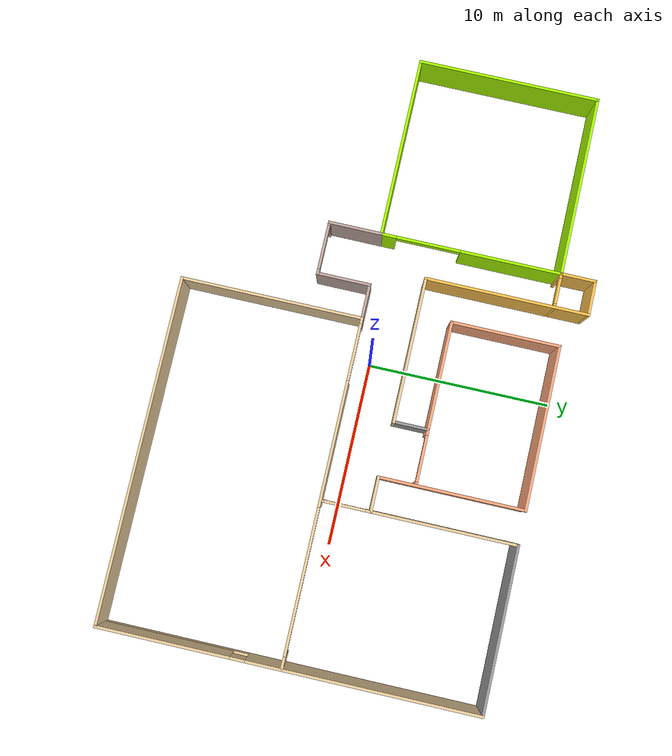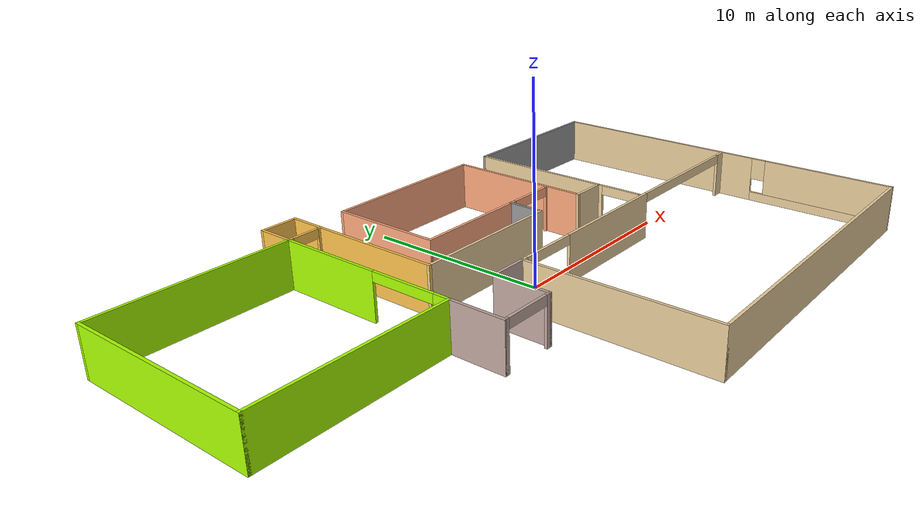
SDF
<?xml version='1.0'?>
<sdf version='1.6'>
  <model name='myhouse'>
    <link name='Wall_15'>
      <pose frame=''>12.2 9.625 0 0 -0 3.14159</pose>
      <self_collide>0</self_collide>
      <kinematic>0</kinematic>
      <visual name='Wall_15_Visual'>
        <pose frame=''>0 0 1.25 0 -0 0</pose>
        <geometry>
          <box>
            <size>9 0.15 2.5</size>
          </box>
        </geometry>
        <material>
          <script>
            <uri>file://media/materials/scripts/gazebo.material</uri>
            <name>Gazebo/Grey</name>
          </script>
          <ambient>1 1 1 1</ambient>
          <diffuse>0.7 0.7 0.7 1</diffuse>
          <specular>0.01 0.01 0.01 1</specular>
          <emissive>0 0 0 1</emissive>
        </material>
        <cast_shadows>1</cast_shadows>
        <transparency>0</transparency>
      </visual>
      <collision name='Wall_15_Collision'>
        <laser_retro>0</laser_retro>
        <max_contacts>10</max_contacts>
        <pose frame=''>0 0 1.25 0 -0 0</pose>
        <geometry>
          <box>
            <size>9 0.15 2.5</size>
          </box>
        </geometry>
        <surface>
          <friction>
            <ode>
              <mu>1</mu>
              <mu2>1</mu2>
              <fdir1>0 0 0</fdir1>
              <slip1>0</slip1>
              <slip2>0</slip2>
            </ode>
            <torsional>
              <coefficient>1</coefficient>
              <patch_radius>0</patch_radius>
              <surface_radius>0</surface_radius>
              <use_patch_radius>1</use_patch_radius>
              <ode>
                <slip>0</slip>
              </ode>
            </torsional>
          </friction>
          <bounce>
            <restitution_coefficient>0</restitution_coefficient>
            <threshold>1e+06</threshold>
          </bounce>
          <contact>
            <collide_without_contact>0</collide_without_contact>
            <collide_without_contact_bitmask>1</collide_without_contact_bitmask>
            <collide_bitmask>1</collide_bitmask>
            <ode>
              <soft_cfm>0</soft_cfm>
              <soft_erp>0.2</soft_erp>
              <kp>1e+13</kp>
              <kd>1</kd>
              <max_vel>0.01</max_vel>
              <min_depth>0</min_depth>
            </ode>
            <bullet>
              <split_impulse>1</split_impulse>
              <split_impulse_penetration_threshold>-0.01</split_impulse_penetration_threshold>
              <soft_cfm>0</soft_cfm>
              <soft_erp>0.2</soft_erp>
              <kp>1e+13</kp>
              <kd>1</kd>
            </bullet>
          </contact>
        </surface>
      </collision>
    </link>
    <link name='Wall_17'>
      <pose frame=''>7.775 5.7 0 0 0 -1.5708</pose>
      <self_collide>0</self_collide>
      <kinematic>0</kinematic>
      <visual name='Wall_17_Visual'>
        <pose frame=''>0 0 1.25 0 -0 0</pose>
        <geometry>
          <box>
            <size>8 0.15 2.5</size>
          </box>
        </geometry>
        <material>
          <script>
            <uri>file://media/materials/scripts/gazebo.material</uri>
            <name>Gazebo/Grey</name>
          </script>
          <ambient>0.921569 0.807843 0.615686 1</ambient>
          <diffuse>0.7 0.7 0.7 1</diffuse>
          <specular>0.01 0.01 0.01 1</specular>
          <emissive>0 0 0 1</emissive>
        </material>
        <cast_shadows>1</cast_shadows>
        <transparency>0</transparency>
      </visual>
      <collision name='Wall_17_Collision'>
        <laser_retro>0</laser_retro>
        <max_contacts>10</max_contacts>
        <pose frame=''>0 0 1.25 0 -0 0</pose>
        <geometry>
          <box>
            <size>8 0.15 2.5</size>
          </box>
        </geometry>
        <surface>
          <friction>
            <ode>
              <mu>1</mu>
              <mu2>1</mu2>
              <fdir1>0 0 0</fdir1>
              <slip1>0</slip1>
              <slip2>0</slip2>
            </ode>
            <torsional>
              <coefficient>1</coefficient>
              <patch_radius>0</patch_radius>
              <surface_radius>0</surface_radius>
              <use_patch_radius>1</use_patch_radius>
              <ode>
                <slip>0</slip>
              </ode>
            </torsional>
          </friction>
          <bounce>
            <restitution_coefficient>0</restitution_coefficient>
            <threshold>1e+06</threshold>
          </bounce>
          <contact>
            <collide_without_contact>0</collide_without_contact>
            <collide_without_contact_bitmask>1</collide_without_contact_bitmask>
            <collide_bitmask>1</collide_bitmask>
            <ode>
              <soft_cfm>0</soft_cfm>
              <soft_erp>0.2</soft_erp>
              <kp>1e+13</kp>
              <kd>1</kd>
              <max_vel>0.01</max_vel>
              <min_depth>0</min_depth>
            </ode>
            <bullet>
              <split_impulse>1</split_impulse>
              <split_impulse_penetration_threshold>-0.01</split_impulse_penetration_threshold>
              <soft_cfm>0</soft_cfm>
              <soft_erp>0.2</soft_erp>
              <kp>1e+13</kp>
              <kd>1</kd>
            </bullet>
          </contact>
        </surface>
      </collision>
    </link>
    <link name='Wall_19'>
      <pose frame=''>6.85 1.775 0 0 -0 3.14159</pose>
      <self_collide>0</self_collide>
      <kinematic>0</kinematic>
      <visual name='Wall_19_Visual'>
        <pose frame=''>0 0 1.25 0 -0 0</pose>
        <geometry>
          <box>
            <size>2 0.15 2.5</size>
          </box>
        </geometry>
        <material>
          <script>
            <uri>file://media/materials/scripts/gazebo.material</uri>
            <name>Gazebo/Grey</name>
          </script>
          <ambient>0.921569 0.807843 0.615686 1</ambient>
          <diffuse>0.7 0.7 0.7 1</diffuse>
          <specular>0.01 0.01 0.01 1</specular>
          <emissive>0 0 0 1</emissive>
        </material>
        <cast_shadows>1</cast_shadows>
        <transparency>0</transparency>
      </visual>
      <collision name='Wall_19_Collision'>
        <laser_retro>0</laser_retro>
        <max_contacts>10</max_contacts>
        <pose frame=''>0 0 1.25 0 -0 0</pose>
        <geometry>
          <box>
            <size>2 0.15 2.5</size>
          </box>
        </geometry>
        <surface>
          <friction>
            <ode>
              <mu>1</mu>
              <mu2>1</mu2>
              <fdir1>0 0 0</fdir1>
              <slip1>0</slip1>
              <slip2>0</slip2>
            </ode>
            <torsional>
              <coefficient>1</coefficient>
              <patch_radius>0</patch_radius>
              <surface_radius>0</surface_radius>
              <use_patch_radius>1</use_patch_radius>
              <ode>
                <slip>0</slip>
              </ode>
            </torsional>
          </friction>
          <bounce>
            <restitution_coefficient>0</restitution_coefficient>
            <threshold>1e+06</threshold>
          </bounce>
          <contact>
            <collide_without_contact>0</collide_without_contact>
            <collide_without_contact_bitmask>1</collide_without_contact_bitmask>
            <collide_bitmask>1</collide_bitmask>
            <ode>
              <soft_cfm>0</soft_cfm>
              <soft_erp>0.2</soft_erp>
              <kp>1e+13</kp>
              <kd>1</kd>
              <max_vel>0.01</max_vel>
              <min_depth>0</min_depth>
            </ode>
            <bullet>
              <split_impulse>1</split_impulse>
              <split_impulse_penetration_threshold>-0.01</split_impulse_penetration_threshold>
              <soft_cfm>0</soft_cfm>
              <soft_erp>0.2</soft_erp>
              <kp>1e+13</kp>
              <kd>1</kd>
            </bullet>
          </contact>
        </surface>
      </collision>
    </link>
    <link name='Wall_20'>
      <pose frame=''>5.925 5.7 0 0 -0 1.5708</pose>
      <self_collide>0</self_collide>
      <kinematic>0</kinematic>
      <visual name='Wall_20_Visual'>
        <pose frame=''>0 0 1.25 0 -0 0</pose>
        <geometry>
          <box>
            <size>8 0.15 2.5</size>
          </box>
        </geometry>
        <material>
          <script>
            <uri>file://media/materials/scripts/gazebo.material</uri>
            <name>Gazebo/Grey</name>
          </script>
          <ambient>1 0.666667 0.498039 1</ambient>
          <diffuse>0.7 0.7 0.7 1</diffuse>
          <specular>0.01 0.01 0.01 1</specular>
          <emissive>0 0 0 1</emissive>
        </material>
        <cast_shadows>1</cast_shadows>
        <transparency>0</transparency>
      </visual>
      <collision name='Wall_20_Collision'>
        <laser_retro>0</laser_retro>
        <max_contacts>10</max_contacts>
        <pose frame=''>0 0 1.25 0 -0 0</pose>
        <geometry>
          <box>
            <size>8 0.15 2.5</size>
          </box>
        </geometry>
        <surface>
          <friction>
            <ode>
              <mu>1</mu>
              <mu2>1</mu2>
              <fdir1>0 0 0</fdir1>
              <slip1>0</slip1>
              <slip2>0</slip2>
            </ode>
            <torsional>
              <coefficient>1</coefficient>
              <patch_radius>0</patch_radius>
              <surface_radius>0</surface_radius>
              <use_patch_radius>1</use_patch_radius>
              <ode>
                <slip>0</slip>
              </ode>
            </torsional>
          </friction>
          <bounce>
            <restitution_coefficient>0</restitution_coefficient>
            <threshold>1e+06</threshold>
          </bounce>
          <contact>
            <collide_without_contact>0</collide_without_contact>
            <collide_without_contact_bitmask>1</collide_without_contact_bitmask>
            <collide_bitmask>1</collide_bitmask>
            <ode>
              <soft_cfm>0</soft_cfm>
              <soft_erp>0.2</soft_erp>
              <kp>1e+13</kp>
              <kd>1</kd>
              <max_vel>0.01</max_vel>
              <min_depth>0</min_depth>
            </ode>
            <bullet>
              <split_impulse>1</split_impulse>
              <split_impulse_penetration_threshold>-0.01</split_impulse_penetration_threshold>
              <soft_cfm>0</soft_cfm>
              <soft_erp>0.2</soft_erp>
              <kp>1e+13</kp>
              <kd>1</kd>
            </bullet>
          </contact>
        </surface>
      </collision>
    </link>
    <link name='Wall_22'>
      <pose frame=''>1.5 9.625 0 0 -0 3.14159</pose>
      <self_collide>0</self_collide>
      <kinematic>0</kinematic>
      <visual name='Wall_22_Visual'>
        <pose frame=''>0 0 1.25 0 -0 0</pose>
        <geometry>
          <box>
            <size>9 0.15 2.5</size>
          </box>
        </geometry>
        <material>
          <script>
            <uri>file://media/materials/scripts/gazebo.material</uri>
            <name>Gazebo/Grey</name>
          </script>
          <ambient>1 0.666667 0.498039 1</ambient>
          <diffuse>0.7 0.7 0.7 1</diffuse>
          <specular>0.01 0.01 0.01 1</specular>
          <emissive>0 0 0 1</emissive>
        </material>
        <cast_shadows>1</cast_shadows>
        <transparency>0</transparency>
      </visual>
      <collision name='Wall_22_Collision'>
        <laser_retro>0</laser_retro>
        <max_contacts>10</max_contacts>
        <pose frame=''>0 0 1.25 0 -0 0</pose>
        <geometry>
          <box>
            <size>9 0.15 2.5</size>
          </box>
        </geometry>
        <surface>
          <friction>
            <ode>
              <mu>1</mu>
              <mu2>1</mu2>
              <fdir1>0 0 0</fdir1>
              <slip1>0</slip1>
              <slip2>0</slip2>
            </ode>
            <torsional>
              <coefficient>1</coefficient>
              <patch_radius>0</patch_radius>
              <surface_radius>0</surface_radius>
              <use_patch_radius>1</use_patch_radius>
              <ode>
                <slip>0</slip>
              </ode>
            </torsional>
          </friction>
          <bounce>
            <restitution_coefficient>0</restitution_coefficient>
            <threshold>1e+06</threshold>
          </bounce>
          <contact>
            <collide_without_contact>0</collide_without_contact>
            <collide_without_contact_bitmask>1</collide_without_contact_bitmask>
            <collide_bitmask>1</collide_bitmask>
            <ode>
              <soft_cfm>0</soft_cfm>
              <soft_erp>0.2</soft_erp>
              <kp>1e+13</kp>
              <kd>1</kd>
              <max_vel>0.01</max_vel>
              <min_depth>0</min_depth>
            </ode>
            <bullet>
              <split_impulse>1</split_impulse>
              <split_impulse_penetration_threshold>-0.01</split_impulse_penetration_threshold>
              <soft_cfm>0</soft_cfm>
              <soft_erp>0.2</soft_erp>
              <kp>1e+13</kp>
              <kd>1</kd>
            </bullet>
          </contact>
        </surface>
      </collision>
    </link>
    <link name='Wall_24'>
      <pose frame=''>-2.925 6.7 0 0 0 -1.5708</pose>
      <self_collide>0</self_collide>
      <kinematic>0</kinematic>
      <visual name='Wall_24_Visual'>
        <pose frame=''>0 0 1.25 0 -0 0</pose>
        <geometry>
          <box>
            <size>6 0.15 2.5</size>
          </box>
        </geometry>
        <material>
          <script>
            <uri>file://media/materials/scripts/gazebo.material</uri>
            <name>Gazebo/Grey</name>
          </script>
          <ambient>1 0.666667 0.498039 1</ambient>
          <diffuse>0.7 0.7 0.7 1</diffuse>
          <specular>0.01 0.01 0.01 1</specular>
          <emissive>0 0 0 1</emissive>
        </material>
        <cast_shadows>1</cast_shadows>
        <transparency>0</transparency>
      </visual>
      <collision name='Wall_24_Collision'>
        <laser_retro>0</laser_retro>
        <max_contacts>10</max_contacts>
        <pose frame=''>0 0 1.25 0 -0 0</pose>
        <geometry>
          <box>
            <size>6 0.15 2.5</size>
          </box>
        </geometry>
        <surface>
          <friction>
            <ode>
              <mu>1</mu>
              <mu2>1</mu2>
              <fdir1>0 0 0</fdir1>
              <slip1>0</slip1>
              <slip2>0</slip2>
            </ode>
            <torsional>
              <coefficient>1</coefficient>
              <patch_radius>0</patch_radius>
              <surface_radius>0</surface_radius>
              <use_patch_radius>1</use_patch_radius>
              <ode>
                <slip>0</slip>
              </ode>
            </torsional>
          </friction>
          <bounce>
            <restitution_coefficient>0</restitution_coefficient>
            <threshold>1e+06</threshold>
          </bounce>
          <contact>
            <collide_without_contact>0</collide_without_contact>
            <collide_without_contact_bitmask>1</collide_without_contact_bitmask>
            <collide_bitmask>1</collide_bitmask>
            <ode>
              <soft_cfm>0</soft_cfm>
              <soft_erp>0.2</soft_erp>
              <kp>1e+13</kp>
              <kd>1</kd>
              <max_vel>0.01</max_vel>
              <min_depth>0</min_depth>
            </ode>
            <bullet>
              <split_impulse>1</split_impulse>
              <split_impulse_penetration_threshold>-0.01</split_impulse_penetration_threshold>
              <soft_cfm>0</soft_cfm>
              <soft_erp>0.2</soft_erp>
              <kp>1e+13</kp>
              <kd>1</kd>
            </bullet>
          </contact>
        </surface>
      </collision>
    </link>
    <link name='Wall_25'>
      <pose frame=''>0 3.775 0 0 -0 0</pose>
      <self_collide>0</self_collide>
      <kinematic>0</kinematic>
      <visual name='Wall_25_Visual'>
        <pose frame=''>0 0 1.25 0 -0 0</pose>
        <geometry>
          <box>
            <size>6 0.15 2.5</size>
          </box>
        </geometry>
        <material>
          <script>
            <uri>file://media/materials/scripts/gazebo.material</uri>
            <name>Gazebo/Grey</name>
          </script>
          <ambient>1 0.666667 0.498039 1</ambient>
          <diffuse>0.7 0.7 0.7 1</diffuse>
          <specular>0.01 0.01 0.01 1</specular>
          <emissive>0 0 0 1</emissive>
        </material>
        <cast_shadows>1</cast_shadows>
        <transparency>0</transparency>
      </visual>
      <collision name='Wall_25_Collision'>
        <laser_retro>0</laser_retro>
        <max_contacts>10</max_contacts>
        <pose frame=''>0 0 1.25 0 -0 0</pose>
        <geometry>
          <box>
            <size>6 0.15 2.5</size>
          </box>
        </geometry>
        <surface>
          <friction>
            <ode>
              <mu>1</mu>
              <mu2>1</mu2>
              <fdir1>0 0 0</fdir1>
              <slip1>0</slip1>
              <slip2>0</slip2>
            </ode>
            <torsional>
              <coefficient>1</coefficient>
              <patch_radius>0</patch_radius>
              <surface_radius>0</surface_radius>
              <use_patch_radius>1</use_patch_radius>
              <ode>
                <slip>0</slip>
              </ode>
            </torsional>
          </friction>
          <bounce>
            <restitution_coefficient>0</restitution_coefficient>
            <threshold>1e+06</threshold>
          </bounce>
          <contact>
            <collide_without_contact>0</collide_without_contact>
            <collide_without_contact_bitmask>1</collide_without_contact_bitmask>
            <collide_bitmask>1</collide_bitmask>
            <ode>
              <soft_cfm>0</soft_cfm>
              <soft_erp>0.2</soft_erp>
              <kp>1e+13</kp>
              <kd>1</kd>
              <max_vel>0.01</max_vel>
              <min_depth>0</min_depth>
            </ode>
            <bullet>
              <split_impulse>1</split_impulse>
              <split_impulse_penetration_threshold>-0.01</split_impulse_penetration_threshold>
              <soft_cfm>0</soft_cfm>
              <soft_erp>0.2</soft_erp>
              <kp>1e+13</kp>
              <kd>1</kd>
            </bullet>
          </contact>
        </surface>
      </collision>
    </link>
    <link name='Wall_26'>
      <pose frame=''>2.925 2.85 0 0 0 -1.5708</pose>
      <self_collide>0</self_collide>
      <kinematic>0</kinematic>
      <visual name='Wall_26_Visual'>
        <pose frame=''>0 0 1.25 0 -0 0</pose>
        <geometry>
          <box>
            <size>2 0.15 2.5</size>
          </box>
        </geometry>
        <material>
          <script>
            <uri>file://media/materials/scripts/gazebo.material</uri>
            <name>Gazebo/Grey</name>
          </script>
          <ambient>1 1 1 1</ambient>
          <diffuse>0.7 0.7 0.7 1</diffuse>
          <specular>0.01 0.01 0.01 1</specular>
          <emissive>0 0 0 1</emissive>
        </material>
        <cast_shadows>1</cast_shadows>
        <transparency>0</transparency>
      </visual>
      <collision name='Wall_26_Collision'>
        <laser_retro>0</laser_retro>
        <max_contacts>10</max_contacts>
        <pose frame=''>0 0 1.25 0 -0 0</pose>
        <geometry>
          <box>
            <size>2 0.15 2.5</size>
          </box>
        </geometry>
        <surface>
          <friction>
            <ode>
              <mu>1</mu>
              <mu2>1</mu2>
              <fdir1>0 0 0</fdir1>
              <slip1>0</slip1>
              <slip2>0</slip2>
            </ode>
            <torsional>
              <coefficient>1</coefficient>
              <patch_radius>0</patch_radius>
              <surface_radius>0</surface_radius>
              <use_patch_radius>1</use_patch_radius>
              <ode>
                <slip>0</slip>
              </ode>
            </torsional>
          </friction>
          <bounce>
            <restitution_coefficient>0</restitution_coefficient>
            <threshold>1e+06</threshold>
          </bounce>
          <contact>
            <collide_without_contact>0</collide_without_contact>
            <collide_without_contact_bitmask>1</collide_without_contact_bitmask>
            <collide_bitmask>1</collide_bitmask>
            <ode>
              <soft_cfm>0</soft_cfm>
              <soft_erp>0.2</soft_erp>
              <kp>1e+13</kp>
              <kd>1</kd>
              <max_vel>0.01</max_vel>
              <min_depth>0</min_depth>
            </ode>
            <bullet>
              <split_impulse>1</split_impulse>
              <split_impulse_penetration_threshold>-0.01</split_impulse_penetration_threshold>
              <soft_cfm>0</soft_cfm>
              <soft_erp>0.2</soft_erp>
              <kp>1e+13</kp>
              <kd>1</kd>
            </bullet>
          </contact>
        </surface>
      </collision>
    </link>
    <link name='Wall_27'>
      <pose frame=''>-1 1.925 0 0 -0 3.14159</pose>
      <self_collide>0</self_collide>
      <kinematic>0</kinematic>
      <visual name='Wall_27_Visual'>
        <pose frame=''>0 0 1.25 0 -0 0</pose>
        <geometry>
          <box>
            <size>8 0.15 2.5</size>
          </box>
        </geometry>
        <material>
          <script>
            <uri>file://media/materials/scripts/gazebo.material</uri>
            <name>Gazebo/Grey</name>
          </script>
          <ambient>0.921569 0.807843 0.615686 1</ambient>
          <diffuse>0.7 0.7 0.7 1</diffuse>
          <specular>0.01 0.01 0.01 1</specular>
          <emissive>0 0 0 1</emissive>
        </material>
        <cast_shadows>1</cast_shadows>
        <transparency>0</transparency>
      </visual>
      <collision name='Wall_27_Collision'>
        <laser_retro>0</laser_retro>
        <max_contacts>10</max_contacts>
        <pose frame=''>0 0 1.25 0 -0 0</pose>
        <geometry>
          <box>
            <size>8 0.15 2.5</size>
          </box>
        </geometry>
        <surface>
          <friction>
            <ode>
              <mu>1</mu>
              <mu2>1</mu2>
              <fdir1>0 0 0</fdir1>
              <slip1>0</slip1>
              <slip2>0</slip2>
            </ode>
            <torsional>
              <coefficient>1</coefficient>
              <patch_radius>0</patch_radius>
              <surface_radius>0</surface_radius>
              <use_patch_radius>1</use_patch_radius>
              <ode>
                <slip>0</slip>
              </ode>
            </torsional>
          </friction>
          <bounce>
            <restitution_coefficient>0</restitution_coefficient>
            <threshold>1e+06</threshold>
          </bounce>
          <contact>
            <collide_without_contact>0</collide_without_contact>
            <collide_without_contact_bitmask>1</collide_without_contact_bitmask>
            <collide_bitmask>1</collide_bitmask>
            <ode>
              <soft_cfm>0</soft_cfm>
              <soft_erp>0.2</soft_erp>
              <kp>1e+13</kp>
              <kd>1</kd>
              <max_vel>0.01</max_vel>
              <min_depth>0</min_depth>
            </ode>
            <bullet>
              <split_impulse>1</split_impulse>
              <split_impulse_penetration_threshold>-0.01</split_impulse_penetration_threshold>
              <soft_cfm>0</soft_cfm>
              <soft_erp>0.2</soft_erp>
              <kp>1e+13</kp>
              <kd>1</kd>
            </bullet>
          </contact>
        </surface>
      </collision>
    </link>
    <link name='Wall_28'>
      <pose frame=''>-4.925 6.35 0 0 -0 1.5708</pose>
      <self_collide>0</self_collide>
      <kinematic>0</kinematic>
      <visual name='Wall_28_Visual'>
        <pose frame=''>0 0 1.25 0 -0 0</pose>
        <geometry>
          <box>
            <size>9 0.15 2.5</size>
          </box>
        </geometry>
        <material>
          <script>
            <uri>file://media/materials/scripts/gazebo.material</uri>
            <name>Gazebo/Grey</name>
          </script>
          <ambient>1 0.764706 0.305882 1</ambient>
          <diffuse>0.7 0.7 0.7 1</diffuse>
          <specular>0.01 0.01 0.01 1</specular>
          <emissive>0 0 0 1</emissive>
        </material>
        <cast_shadows>1</cast_shadows>
        <transparency>0</transparency>
      </visual>
      <collision name='Wall_28_Collision'>
        <laser_retro>0</laser_retro>
        <max_contacts>10</max_contacts>
        <pose frame=''>0 0 1.25 0 -0 0</pose>
        <geometry>
          <box>
            <size>9 0.15 2.5</size>
          </box>
        </geometry>
        <surface>
          <friction>
            <ode>
              <mu>1</mu>
              <mu2>1</mu2>
              <fdir1>0 0 0</fdir1>
              <slip1>0</slip1>
              <slip2>0</slip2>
            </ode>
            <torsional>
              <coefficient>1</coefficient>
              <patch_radius>0</patch_radius>
              <surface_radius>0</surface_radius>
              <use_patch_radius>1</use_patch_radius>
              <ode>
                <slip>0</slip>
              </ode>
            </torsional>
          </friction>
          <bounce>
            <restitution_coefficient>0</restitution_coefficient>
            <threshold>1e+06</threshold>
          </bounce>
          <contact>
            <collide_without_contact>0</collide_without_contact>
            <collide_without_contact_bitmask>1</collide_without_contact_bitmask>
            <collide_bitmask>1</collide_bitmask>
            <ode>
              <soft_cfm>0</soft_cfm>
              <soft_erp>0.2</soft_erp>
              <kp>1e+13</kp>
              <kd>1</kd>
              <max_vel>0.01</max_vel>
              <min_depth>0</min_depth>
            </ode>
            <bullet>
              <split_impulse>1</split_impulse>
              <split_impulse_penetration_threshold>-0.01</split_impulse_penetration_threshold>
              <soft_cfm>0</soft_cfm>
              <soft_erp>0.2</soft_erp>
              <kp>1e+13</kp>
              <kd>1</kd>
            </bullet>
          </contact>
        </surface>
      </collision>
    </link>
    <link name='Wall_29'>
      <pose frame=''>-5.85 10.775 0 0 -0 3.14159</pose>
      <self_collide>0</self_collide>
      <kinematic>0</kinematic>
      <visual name='Wall_29_Visual'>
        <pose frame=''>0 0 1.25 0 -0 0</pose>
        <geometry>
          <box>
            <size>2 0.15 2.5</size>
          </box>
        </geometry>
        <material>
          <script>
            <uri>file://media/materials/scripts/gazebo.material</uri>
            <name>Gazebo/Grey</name>
          </script>
          <ambient>1 0.764706 0.305882 1</ambient>
          <diffuse>0.7 0.7 0.7 1</diffuse>
          <specular>0.01 0.01 0.01 1</specular>
          <emissive>0 0 0 1</emissive>
        </material>
        <cast_shadows>1</cast_shadows>
        <transparency>0</transparency>
      </visual>
      <collision name='Wall_29_Collision'>
        <laser_retro>0</laser_retro>
        <max_contacts>10</max_contacts>
        <pose frame=''>0 0 1.25 0 -0 0</pose>
        <geometry>
          <box>
            <size>2 0.15 2.5</size>
          </box>
        </geometry>
        <surface>
          <friction>
            <ode>
              <mu>1</mu>
              <mu2>1</mu2>
              <fdir1>0 0 0</fdir1>
              <slip1>0</slip1>
              <slip2>0</slip2>
            </ode>
            <torsional>
              <coefficient>1</coefficient>
              <patch_radius>0</patch_radius>
              <surface_radius>0</surface_radius>
              <use_patch_radius>1</use_patch_radius>
              <ode>
                <slip>0</slip>
              </ode>
            </torsional>
          </friction>
          <bounce>
            <restitution_coefficient>0</restitution_coefficient>
            <threshold>1e+06</threshold>
          </bounce>
          <contact>
            <collide_without_contact>0</collide_without_contact>
            <collide_without_contact_bitmask>1</collide_without_contact_bitmask>
            <collide_bitmask>1</collide_bitmask>
            <ode>
              <soft_cfm>0</soft_cfm>
              <soft_erp>0.2</soft_erp>
              <kp>1e+13</kp>
              <kd>1</kd>
              <max_vel>0.01</max_vel>
              <min_depth>0</min_depth>
            </ode>
            <bullet>
              <split_impulse>1</split_impulse>
              <split_impulse_penetration_threshold>-0.01</split_impulse_penetration_threshold>
              <soft_cfm>0</soft_cfm>
              <soft_erp>0.2</soft_erp>
              <kp>1e+13</kp>
              <kd>1</kd>
            </bullet>
          </contact>
        </surface>
      </collision>
    </link>
    <link name='Wall_30'>
      <pose frame=''>-6.775 9.85 0 0 0 -1.5708</pose>
      <self_collide>0</self_collide>
      <kinematic>0</kinematic>
      <visual name='Wall_30_Visual'>
        <pose frame=''>0 0 1.25 0 -0 0</pose>
        <geometry>
          <box>
            <size>2 0.15 2.5</size>
          </box>
        </geometry>
        <material>
          <script>
            <uri>file://media/materials/scripts/gazebo.material</uri>
            <name>Gazebo/Grey</name>
          </script>
          <ambient>1 0.764706 0.305882 1</ambient>
          <diffuse>0.7 0.7 0.7 1</diffuse>
          <specular>0.01 0.01 0.01 1</specular>
          <emissive>0 0 0 1</emissive>
        </material>
        <cast_shadows>1</cast_shadows>
        <transparency>0</transparency>
      </visual>
      <collision name='Wall_30_Collision'>
        <laser_retro>0</laser_retro>
        <max_contacts>10</max_contacts>
        <pose frame=''>0 0 1.25 0 -0 0</pose>
        <geometry>
          <box>
            <size>2 0.15 2.5</size>
          </box>
        </geometry>
        <surface>
          <friction>
            <ode>
              <mu>1</mu>
              <mu2>1</mu2>
              <fdir1>0 0 0</fdir1>
              <slip1>0</slip1>
              <slip2>0</slip2>
            </ode>
            <torsional>
              <coefficient>1</coefficient>
              <patch_radius>0</patch_radius>
              <surface_radius>0</surface_radius>
              <use_patch_radius>1</use_patch_radius>
              <ode>
                <slip>0</slip>
              </ode>
            </torsional>
          </friction>
          <bounce>
            <restitution_coefficient>0</restitution_coefficient>
            <threshold>1e+06</threshold>
          </bounce>
          <contact>
            <collide_without_contact>0</collide_without_contact>
            <collide_without_contact_bitmask>1</collide_without_contact_bitmask>
            <collide_bitmask>1</collide_bitmask>
            <ode>
              <soft_cfm>0</soft_cfm>
              <soft_erp>0.2</soft_erp>
              <kp>1e+13</kp>
              <kd>1</kd>
              <max_vel>0.01</max_vel>
              <min_depth>0</min_depth>
            </ode>
            <bullet>
              <split_impulse>1</split_impulse>
              <split_impulse_penetration_threshold>-0.01</split_impulse_penetration_threshold>
              <soft_cfm>0</soft_cfm>
              <soft_erp>0.2</soft_erp>
              <kp>1e+13</kp>
              <kd>1</kd>
            </bullet>
          </contact>
        </surface>
      </collision>
    </link>
    <link name='Wall_31'>
      <pose frame=''>-11.7 8.925 0 0 -0 3.14159</pose>
      <self_collide>0</self_collide>
      <kinematic>0</kinematic>
      <visual name='Wall_31_Visual'>
        <pose frame=''>0 0 1.25 0 -0 0</pose>
        <geometry>
          <box>
            <size>10 0.15 2.5</size>
          </box>
        </geometry>
        <material>
          <script>
            <uri>file://media/materials/scripts/gazebo.material</uri>
            <name>Gazebo/Grey</name>
          </script>
          <ambient>0.666667 1 0 1</ambient>
          <diffuse>0.7 0.7 0.7 1</diffuse>
          <specular>0.01 0.01 0.01 1</specular>
          <emissive>0 0 0 1</emissive>
        </material>
        <cast_shadows>1</cast_shadows>
        <transparency>0</transparency>
      </visual>
      <collision name='Wall_31_Collision'>
        <laser_retro>0</laser_retro>
        <max_contacts>10</max_contacts>
        <pose frame=''>0 0 1.25 0 -0 0</pose>
        <geometry>
          <box>
            <size>10 0.15 2.5</size>
          </box>
        </geometry>
        <surface>
          <friction>
            <ode>
              <mu>1</mu>
              <mu2>1</mu2>
              <fdir1>0 0 0</fdir1>
              <slip1>0</slip1>
              <slip2>0</slip2>
            </ode>
            <torsional>
              <coefficient>1</coefficient>
              <patch_radius>0</patch_radius>
              <surface_radius>0</surface_radius>
              <use_patch_radius>1</use_patch_radius>
              <ode>
                <slip>0</slip>
              </ode>
            </torsional>
          </friction>
          <bounce>
            <restitution_coefficient>0</restitution_coefficient>
            <threshold>1e+06</threshold>
          </bounce>
          <contact>
            <collide_without_contact>0</collide_without_contact>
            <collide_without_contact_bitmask>1</collide_without_contact_bitmask>
            <collide_bitmask>1</collide_bitmask>
            <ode>
              <soft_cfm>0</soft_cfm>
              <soft_erp>0.2</soft_erp>
              <kp>1e+13</kp>
              <kd>1</kd>
              <max_vel>0.01</max_vel>
              <min_depth>0</min_depth>
            </ode>
            <bullet>
              <split_impulse>1</split_impulse>
              <split_impulse_penetration_threshold>-0.01</split_impulse_penetration_threshold>
              <soft_cfm>0</soft_cfm>
              <soft_erp>0.2</soft_erp>
              <kp>1e+13</kp>
              <kd>1</kd>
            </bullet>
          </contact>
        </surface>
      </collision>
    </link>
    <link name='Wall_32'>
      <pose frame=''>-16.625 4 0 0 0 -1.5708</pose>
      <self_collide>0</self_collide>
      <kinematic>0</kinematic>
      <visual name='Wall_32_Visual'>
        <pose frame=''>0 0 1.25 0 -0 0</pose>
        <geometry>
          <box>
            <size>10 0.15 2.5</size>
          </box>
        </geometry>
        <material>
          <script>
            <uri>file://media/materials/scripts/gazebo.material</uri>
            <name>Gazebo/Grey</name>
          </script>
          <ambient>0.666667 1 0 1</ambient>
          <diffuse>0.7 0.7 0.7 1</diffuse>
          <specular>0.01 0.01 0.01 1</specular>
          <emissive>0 0 0 1</emissive>
        </material>
        <cast_shadows>1</cast_shadows>
        <transparency>0</transparency>
      </visual>
      <collision name='Wall_32_Collision'>
        <laser_retro>0</laser_retro>
        <max_contacts>10</max_contacts>
        <pose frame=''>0 0 1.25 0 -0 0</pose>
        <geometry>
          <box>
            <size>10 0.15 2.5</size>
          </box>
        </geometry>
        <surface>
          <friction>
            <ode>
              <mu>1</mu>
              <mu2>1</mu2>
              <fdir1>0 0 0</fdir1>
              <slip1>0</slip1>
              <slip2>0</slip2>
            </ode>
            <torsional>
              <coefficient>1</coefficient>
              <patch_radius>0</patch_radius>
              <surface_radius>0</surface_radius>
              <use_patch_radius>1</use_patch_radius>
              <ode>
                <slip>0</slip>
              </ode>
            </torsional>
          </friction>
          <bounce>
            <restitution_coefficient>0</restitution_coefficient>
            <threshold>1e+06</threshold>
          </bounce>
          <contact>
            <collide_without_contact>0</collide_without_contact>
            <collide_without_contact_bitmask>1</collide_without_contact_bitmask>
            <collide_bitmask>1</collide_bitmask>
            <ode>
              <soft_cfm>0</soft_cfm>
              <soft_erp>0.2</soft_erp>
              <kp>1e+13</kp>
              <kd>1</kd>
              <max_vel>0.01</max_vel>
              <min_depth>0</min_depth>
            </ode>
            <bullet>
              <split_impulse>1</split_impulse>
              <split_impulse_penetration_threshold>-0.01</split_impulse_penetration_threshold>
              <soft_cfm>0</soft_cfm>
              <soft_erp>0.2</soft_erp>
              <kp>1e+13</kp>
              <kd>1</kd>
            </bullet>
          </contact>
        </surface>
      </collision>
    </link>
    <link name='Wall_33'>
      <pose frame=''>-11.7 -0.924999 0 0 -0 0</pose>
      <self_collide>0</self_collide>
      <kinematic>0</kinematic>
      <visual name='Wall_33_Visual'>
        <pose frame=''>0 0 1.25 0 -0 0</pose>
        <geometry>
          <box>
            <size>10 0.15 2.5</size>
          </box>
        </geometry>
        <material>
          <script>
            <uri>file://media/materials/scripts/gazebo.material</uri>
            <name>Gazebo/Grey</name>
          </script>
          <ambient>0.666667 1 0 1</ambient>
          <diffuse>0.7 0.7 0.7 1</diffuse>
          <specular>0.01 0.01 0.01 1</specular>
          <emissive>0 0 0 1</emissive>
        </material>
        <cast_shadows>1</cast_shadows>
        <transparency>0</transparency>
      </visual>
      <collision name='Wall_33_Collision'>
        <laser_retro>0</laser_retro>
        <max_contacts>10</max_contacts>
        <pose frame=''>0 0 1.25 0 -0 0</pose>
        <geometry>
          <box>
            <size>10 0.15 2.5</size>
          </box>
        </geometry>
        <surface>
          <friction>
            <ode>
              <mu>1</mu>
              <mu2>1</mu2>
              <fdir1>0 0 0</fdir1>
              <slip1>0</slip1>
              <slip2>0</slip2>
            </ode>
            <torsional>
              <coefficient>1</coefficient>
              <patch_radius>0</patch_radius>
              <surface_radius>0</surface_radius>
              <use_patch_radius>1</use_patch_radius>
              <ode>
                <slip>0</slip>
              </ode>
            </torsional>
          </friction>
          <bounce>
            <restitution_coefficient>0</restitution_coefficient>
            <threshold>1e+06</threshold>
          </bounce>
          <contact>
            <collide_without_contact>0</collide_without_contact>
            <collide_without_contact_bitmask>1</collide_without_contact_bitmask>
            <collide_bitmask>1</collide_bitmask>
            <ode>
              <soft_cfm>0</soft_cfm>
              <soft_erp>0.2</soft_erp>
              <kp>1e+13</kp>
              <kd>1</kd>
              <max_vel>0.01</max_vel>
              <min_depth>0</min_depth>
            </ode>
            <bullet>
              <split_impulse>1</split_impulse>
              <split_impulse_penetration_threshold>-0.01</split_impulse_penetration_threshold>
              <soft_cfm>0</soft_cfm>
              <soft_erp>0.2</soft_erp>
              <kp>1e+13</kp>
              <kd>1</kd>
            </bullet>
          </contact>
        </surface>
      </collision>
    </link>
    <link name='Wall_34'>
      <pose frame=''>-6.775 -2.35 0 0 0 -1.5708</pose>
      <self_collide>0</self_collide>
      <kinematic>0</kinematic>
      <visual name='Wall_34_Visual'>
        <pose frame=''>0 0 1.25 0 -0 0</pose>
        <geometry>
          <box>
            <size>3 0.15 2.5</size>
          </box>
        </geometry>
        <material>
          <script>
            <uri>file://media/materials/scripts/gazebo.material</uri>
            <name>Gazebo/Grey</name>
          </script>
          <ambient>0.760784 0.662745 0.627451 1</ambient>
          <diffuse>0.7 0.7 0.7 1</diffuse>
          <specular>0.01 0.01 0.01 1</specular>
          <emissive>0 0 0 1</emissive>
        </material>
        <cast_shadows>1</cast_shadows>
        <transparency>0</transparency>
      </visual>
      <collision name='Wall_34_Collision'>
        <laser_retro>0</laser_retro>
        <max_contacts>10</max_contacts>
        <pose frame=''>0 0 1.25 0 -0 0</pose>
        <geometry>
          <box>
            <size>3 0.15 2.5</size>
          </box>
        </geometry>
        <surface>
          <friction>
            <ode>
              <mu>1</mu>
              <mu2>1</mu2>
              <fdir1>0 0 0</fdir1>
              <slip1>0</slip1>
              <slip2>0</slip2>
            </ode>
            <torsional>
              <coefficient>1</coefficient>
              <patch_radius>0</patch_radius>
              <surface_radius>0</surface_radius>
              <use_patch_radius>1</use_patch_radius>
              <ode>
                <slip>0</slip>
              </ode>
            </torsional>
          </friction>
          <bounce>
            <restitution_coefficient>0</restitution_coefficient>
            <threshold>1e+06</threshold>
          </bounce>
          <contact>
            <collide_without_contact>0</collide_without_contact>
            <collide_without_contact_bitmask>1</collide_without_contact_bitmask>
            <collide_bitmask>1</collide_bitmask>
            <ode>
              <soft_cfm>0</soft_cfm>
              <soft_erp>0.2</soft_erp>
              <kp>1e+13</kp>
              <kd>1</kd>
              <max_vel>0.01</max_vel>
              <min_depth>0</min_depth>
            </ode>
            <bullet>
              <split_impulse>1</split_impulse>
              <split_impulse_penetration_threshold>-0.01</split_impulse_penetration_threshold>
              <soft_cfm>0</soft_cfm>
              <soft_erp>0.2</soft_erp>
              <kp>1e+13</kp>
              <kd>1</kd>
            </bullet>
          </contact>
        </surface>
      </collision>
    </link>
    <link name='Wall_35'>
      <pose frame=''>-5.35 -3.775 0 0 -0 0</pose>
      <self_collide>0</self_collide>
      <kinematic>0</kinematic>
      <visual name='Wall_35_Visual_0'>
        <pose frame=''>-1.3701 0 1.25 0 -0 0</pose>
        <geometry>
          <box>
            <size>0.259804 0.15 2.5</size>
          </box>
        </geometry>
        <material>
          <script>
            <uri>file://media/materials/scripts/gazebo.material</uri>
            <name>Gazebo/Grey</name>
          </script>
          <ambient>0.760784 0.662745 0.627451 1</ambient>
          <diffuse>0.7 0.7 0.7 1</diffuse>
          <specular>0.01 0.01 0.01 1</specular>
          <emissive>0 0 0 1</emissive>
        </material>
        <cast_shadows>1</cast_shadows>
        <transparency>0</transparency>
      </visual>
      <visual name='Wall_35_Visual_1'>
        <pose frame=''>1.33743 0 1.25 0 -0 0</pose>
        <geometry>
          <box>
            <size>0.325141 0.15 2.5</size>
          </box>
        </geometry>
        <material>
          <script>
            <uri>file://media/materials/scripts/gazebo.material</uri>
            <name>Gazebo/Grey</name>
          </script>
          <ambient>0.760784 0.662745 0.627451 1</ambient>
          <diffuse>0.7 0.7 0.7 1</diffuse>
          <specular>0.01 0.01 0.01 1</specular>
          <emissive>0 0 0 1</emissive>
        </material>
        <cast_shadows>1</cast_shadows>
        <transparency>0</transparency>
      </visual>
      <visual name='Wall_35_Visual_2'>
        <pose frame=''>-0.032669 0 2.25 0 -0 0</pose>
        <geometry>
          <box>
            <size>2.41506 0.15 0.5</size>
          </box>
        </geometry>
        <material>
          <script>
            <uri>file://media/materials/scripts/gazebo.material</uri>
            <name>Gazebo/Grey</name>
          </script>
          <ambient>0.760784 0.662745 0.627451 1</ambient>
          <diffuse>0.7 0.7 0.7 1</diffuse>
          <specular>0.01 0.01 0.01 1</specular>
          <emissive>0 0 0 1</emissive>
        </material>
        <cast_shadows>1</cast_shadows>
        <transparency>0</transparency>
      </visual>
      <collision name='Wall_35_Collision_0'>
        <laser_retro>0</laser_retro>
        <max_contacts>10</max_contacts>
        <pose frame=''>-1.3701 0 1.25 0 -0 0</pose>
        <geometry>
          <box>
            <size>0.259804 0.15 2.5</size>
          </box>
        </geometry>
        <surface>
          <friction>
            <ode>
              <mu>1</mu>
              <mu2>1</mu2>
              <fdir1>0 0 0</fdir1>
              <slip1>0</slip1>
              <slip2>0</slip2>
            </ode>
            <torsional>
              <coefficient>1</coefficient>
              <patch_radius>0</patch_radius>
              <surface_radius>0</surface_radius>
              <use_patch_radius>1</use_patch_radius>
              <ode>
                <slip>0</slip>
              </ode>
            </torsional>
          </friction>
          <bounce>
            <restitution_coefficient>0</restitution_coefficient>
            <threshold>1e+06</threshold>
          </bounce>
          <contact>
            <collide_without_contact>0</collide_without_contact>
            <collide_without_contact_bitmask>1</collide_without_contact_bitmask>
            <collide_bitmask>1</collide_bitmask>
            <ode>
              <soft_cfm>0</soft_cfm>
              <soft_erp>0.2</soft_erp>
              <kp>1e+13</kp>
              <kd>1</kd>
              <max_vel>0.01</max_vel>
              <min_depth>0</min_depth>
            </ode>
            <bullet>
              <split_impulse>1</split_impulse>
              <split_impulse_penetration_threshold>-0.01</split_impulse_penetration_threshold>
              <soft_cfm>0</soft_cfm>
              <soft_erp>0.2</soft_erp>
              <kp>1e+13</kp>
              <kd>1</kd>
            </bullet>
          </contact>
        </surface>
      </collision>
      <collision name='Wall_35_Collision_1'>
        <laser_retro>0</laser_retro>
        <max_contacts>10</max_contacts>
        <pose frame=''>1.33743 0 1.25 0 -0 0</pose>
        <geometry>
          <box>
            <size>0.325141 0.15 2.5</size>
          </box>
        </geometry>
        <surface>
          <friction>
            <ode>
              <mu>1</mu>
              <mu2>1</mu2>
              <fdir1>0 0 0</fdir1>
              <slip1>0</slip1>
              <slip2>0</slip2>
            </ode>
            <torsional>
              <coefficient>1</coefficient>
              <patch_radius>0</patch_radius>
              <surface_radius>0</surface_radius>
              <use_patch_radius>1</use_patch_radius>
              <ode>
                <slip>0</slip>
              </ode>
            </torsional>
          </friction>
          <bounce>
            <restitution_coefficient>0</restitution_coefficient>
            <threshold>1e+06</threshold>
          </bounce>
          <contact>
            <collide_without_contact>0</collide_without_contact>
            <collide_without_contact_bitmask>1</collide_without_contact_bitmask>
            <collide_bitmask>1</collide_bitmask>
            <ode>
              <soft_cfm>0</soft_cfm>
              <soft_erp>0.2</soft_erp>
              <kp>1e+13</kp>
              <kd>1</kd>
              <max_vel>0.01</max_vel>
              <min_depth>0</min_depth>
            </ode>
            <bullet>
              <split_impulse>1</split_impulse>
              <split_impulse_penetration_threshold>-0.01</split_impulse_penetration_threshold>
              <soft_cfm>0</soft_cfm>
              <soft_erp>0.2</soft_erp>
              <kp>1e+13</kp>
              <kd>1</kd>
            </bullet>
          </contact>
        </surface>
      </collision>
      <collision name='Wall_35_Collision_2'>
        <laser_retro>0</laser_retro>
        <max_contacts>10</max_contacts>
        <pose frame=''>-0.032669 0 2.25 0 -0 0</pose>
        <geometry>
          <box>
            <size>2.41506 0.15 0.5</size>
          </box>
        </geometry>
        <surface>
          <friction>
            <ode>
              <mu>1</mu>
              <mu2>1</mu2>
              <fdir1>0 0 0</fdir1>
              <slip1>0</slip1>
              <slip2>0</slip2>
            </ode>
            <torsional>
              <coefficient>1</coefficient>
              <patch_radius>0</patch_radius>
              <surface_radius>0</surface_radius>
              <use_patch_radius>1</use_patch_radius>
              <ode>
                <slip>0</slip>
              </ode>
            </torsional>
          </friction>
          <bounce>
            <restitution_coefficient>0</restitution_coefficient>
            <threshold>1e+06</threshold>
          </bounce>
          <contact>
            <collide_without_contact>0</collide_without_contact>
            <collide_without_contact_bitmask>1</collide_without_contact_bitmask>
            <collide_bitmask>1</collide_bitmask>
            <ode>
              <soft_cfm>0</soft_cfm>
              <soft_erp>0.2</soft_erp>
              <kp>1e+13</kp>
              <kd>1</kd>
              <max_vel>0.01</max_vel>
              <min_depth>0</min_depth>
            </ode>
            <bullet>
              <split_impulse>1</split_impulse>
              <split_impulse_penetration_threshold>-0.01</split_impulse_penetration_threshold>
              <soft_cfm>0</soft_cfm>
              <soft_erp>0.2</soft_erp>
              <kp>1e+13</kp>
              <kd>1</kd>
            </bullet>
          </contact>
        </surface>
      </collision>
    </link>
    <link name='Wall_36'>
      <pose frame=''>-3.925 -2.35 0 0 -0 1.5708</pose>
      <self_collide>0</self_collide>
      <kinematic>0</kinematic>
      <visual name='Wall_36_Visual'>
        <pose frame=''>0 0 1.25 0 -0 0</pose>
        <geometry>
          <box>
            <size>3 0.15 2.5</size>
          </box>
        </geometry>
        <material>
          <script>
            <uri>file://media/materials/scripts/gazebo.material</uri>
            <name>Gazebo/Grey</name>
          </script>
          <ambient>0.760784 0.662745 0.627451 1</ambient>
          <diffuse>0.7 0.7 0.7 1</diffuse>
          <specular>0.01 0.01 0.01 1</specular>
          <emissive>0 0 0 1</emissive>
        </material>
        <cast_shadows>1</cast_shadows>
        <transparency>0</transparency>
      </visual>
      <collision name='Wall_36_Collision'>
        <laser_retro>0</laser_retro>
        <max_contacts>10</max_contacts>
        <pose frame=''>0 0 1.25 0 -0 0</pose>
        <geometry>
          <box>
            <size>3 0.15 2.5</size>
          </box>
        </geometry>
        <surface>
          <friction>
            <ode>
              <mu>1</mu>
              <mu2>1</mu2>
              <fdir1>0 0 0</fdir1>
              <slip1>0</slip1>
              <slip2>0</slip2>
            </ode>
            <torsional>
              <coefficient>1</coefficient>
              <patch_radius>0</patch_radius>
              <surface_radius>0</surface_radius>
              <use_patch_radius>1</use_patch_radius>
              <ode>
                <slip>0</slip>
              </ode>
            </torsional>
          </friction>
          <bounce>
            <restitution_coefficient>0</restitution_coefficient>
            <threshold>1e+06</threshold>
          </bounce>
          <contact>
            <collide_without_contact>0</collide_without_contact>
            <collide_without_contact_bitmask>1</collide_without_contact_bitmask>
            <collide_bitmask>1</collide_bitmask>
            <ode>
              <soft_cfm>0</soft_cfm>
              <soft_erp>0.2</soft_erp>
              <kp>1e+13</kp>
              <kd>1</kd>
              <max_vel>0.01</max_vel>
              <min_depth>0</min_depth>
            </ode>
            <bullet>
              <split_impulse>1</split_impulse>
              <split_impulse_penetration_threshold>-0.01</split_impulse_penetration_threshold>
              <soft_cfm>0</soft_cfm>
              <soft_erp>0.2</soft_erp>
              <kp>1e+13</kp>
              <kd>1</kd>
            </bullet>
          </contact>
        </surface>
      </collision>
    </link>
    <link name='Wall_37'>
      <pose frame=''>-3 -0.924999 0 0 -0 0</pose>
      <self_collide>0</self_collide>
      <kinematic>0</kinematic>
      <visual name='Wall_37_Visual'>
        <pose frame=''>0 0 1.25 0 -0 0</pose>
        <geometry>
          <box>
            <size>2 0.15 2.5</size>
          </box>
        </geometry>
        <material>
          <script>
            <uri>file://media/materials/scripts/gazebo.material</uri>
            <name>Gazebo/Grey</name>
          </script>
          <ambient>0.760784 0.662745 0.627451 1</ambient>
          <diffuse>0.7 0.7 0.7 1</diffuse>
          <specular>0.01 0.01 0.01 1</specular>
          <emissive>0 0 0 1</emissive>
        </material>
        <cast_shadows>1</cast_shadows>
        <transparency>0</transparency>
      </visual>
      <collision name='Wall_37_Collision'>
        <laser_retro>0</laser_retro>
        <max_contacts>10</max_contacts>
        <pose frame=''>0 0 1.25 0 -0 0</pose>
        <geometry>
          <box>
            <size>2 0.15 2.5</size>
          </box>
        </geometry>
        <surface>
          <friction>
            <ode>
              <mu>1</mu>
              <mu2>1</mu2>
              <fdir1>0 0 0</fdir1>
              <slip1>0</slip1>
              <slip2>0</slip2>
            </ode>
            <torsional>
              <coefficient>1</coefficient>
              <patch_radius>0</patch_radius>
              <surface_radius>0</surface_radius>
              <use_patch_radius>1</use_patch_radius>
              <ode>
                <slip>0</slip>
              </ode>
            </torsional>
          </friction>
          <bounce>
            <restitution_coefficient>0</restitution_coefficient>
            <threshold>1e+06</threshold>
          </bounce>
          <contact>
            <collide_without_contact>0</collide_without_contact>
            <collide_without_contact_bitmask>1</collide_without_contact_bitmask>
            <collide_bitmask>1</collide_bitmask>
            <ode>
              <soft_cfm>0</soft_cfm>
              <soft_erp>0.2</soft_erp>
              <kp>1e+13</kp>
              <kd>1</kd>
              <max_vel>0.01</max_vel>
              <min_depth>0</min_depth>
            </ode>
            <bullet>
              <split_impulse>1</split_impulse>
              <split_impulse_penetration_threshold>-0.01</split_impulse_penetration_threshold>
              <soft_cfm>0</soft_cfm>
              <soft_erp>0.2</soft_erp>
              <kp>1e+13</kp>
              <kd>1</kd>
            </bullet>
          </contact>
        </surface>
      </collision>
    </link>
    <link name='Wall_40'>
      <pose frame=''>16.625 -0.575 0 0 0 -1.5708</pose>
      <self_collide>0</self_collide>
      <kinematic>0</kinematic>
      <visual name='Wall_40_Visual_0'>
        <pose frame=''>-3.99354 0 1.25 0 -0 0</pose>
        <geometry>
          <box>
            <size>12.5629 0.15 2.5</size>
          </box>
        </geometry>
        <material>
          <script>
            <uri>file://media/materials/scripts/gazebo.material</uri>
            <name>Gazebo/Grey</name>
          </script>
          <ambient>0.921569 0.807843 0.615686 1</ambient>
          <diffuse>0.7 0.7 0.7 1</diffuse>
          <specular>0.01 0.01 0.01 1</specular>
          <emissive>0 0 0 1</emissive>
        </material>
        <cast_shadows>1</cast_shadows>
        <transparency>0</transparency>
      </visual>
      <visual name='Wall_40_Visual_1'>
        <pose frame=''>6.28146 0 0.25 0 -0 0</pose>
        <geometry>
          <box>
            <size>7.98707 0.15 0.5</size>
          </box>
        </geometry>
        <material>
          <script>
            <uri>file://media/materials/scripts/gazebo.material</uri>
            <name>Gazebo/Grey</name>
          </script>
          <ambient>0.921569 0.807843 0.615686 1</ambient>
          <diffuse>0.7 0.7 0.7 1</diffuse>
          <specular>0.01 0.01 0.01 1</specular>
          <emissive>0 0 0 1</emissive>
        </material>
        <cast_shadows>1</cast_shadows>
        <transparency>0</transparency>
      </visual>
      <visual name='Wall_40_Visual_2'>
        <pose frame=''>6.68146 0 1.5 0 -0 0</pose>
        <geometry>
          <box>
            <size>7.18707 0.15 2</size>
          </box>
        </geometry>
        <material>
          <script>
            <uri>file://media/materials/scripts/gazebo.material</uri>
            <name>Gazebo/Grey</name>
          </script>
          <ambient>0.921569 0.807843 0.615686 1</ambient>
          <diffuse>0.7 0.7 0.7 1</diffuse>
          <specular>0.01 0.01 0.01 1</specular>
          <emissive>0 0 0 1</emissive>
        </material>
        <cast_shadows>1</cast_shadows>
        <transparency>0</transparency>
      </visual>
      <visual name='Wall_40_Visual_3'>
        <pose frame=''>2.68793 0 1.9 0 -0 0</pose>
        <geometry>
          <box>
            <size>0.8 0.15 1.2</size>
          </box>
        </geometry>
        <material>
          <script>
            <uri>file://media/materials/scripts/gazebo.material</uri>
            <name>Gazebo/Grey</name>
          </script>
          <ambient>0.921569 0.807843 0.615686 1</ambient>
          <diffuse>0.7 0.7 0.7 1</diffuse>
          <specular>0.01 0.01 0.01 1</specular>
          <emissive>0 0 0 1</emissive>
        </material>
        <cast_shadows>1</cast_shadows>
        <transparency>0</transparency>
      </visual>
      <collision name='Wall_40_Collision_0'>
        <laser_retro>0</laser_retro>
        <max_contacts>10</max_contacts>
        <pose frame=''>-3.99354 0 1.25 0 -0 0</pose>
        <geometry>
          <box>
            <size>12.5629 0.15 2.5</size>
          </box>
        </geometry>
        <surface>
          <friction>
            <ode>
              <mu>1</mu>
              <mu2>1</mu2>
              <fdir1>0 0 0</fdir1>
              <slip1>0</slip1>
              <slip2>0</slip2>
            </ode>
            <torsional>
              <coefficient>1</coefficient>
              <patch_radius>0</patch_radius>
              <surface_radius>0</surface_radius>
              <use_patch_radius>1</use_patch_radius>
              <ode>
                <slip>0</slip>
              </ode>
            </torsional>
          </friction>
          <bounce>
            <restitution_coefficient>0</restitution_coefficient>
            <threshold>1e+06</threshold>
          </bounce>
          <contact>
            <collide_without_contact>0</collide_without_contact>
            <collide_without_contact_bitmask>1</collide_without_contact_bitmask>
            <collide_bitmask>1</collide_bitmask>
            <ode>
              <soft_cfm>0</soft_cfm>
              <soft_erp>0.2</soft_erp>
              <kp>1e+13</kp>
              <kd>1</kd>
              <max_vel>0.01</max_vel>
              <min_depth>0</min_depth>
            </ode>
            <bullet>
              <split_impulse>1</split_impulse>
              <split_impulse_penetration_threshold>-0.01</split_impulse_penetration_threshold>
              <soft_cfm>0</soft_cfm>
              <soft_erp>0.2</soft_erp>
              <kp>1e+13</kp>
              <kd>1</kd>
            </bullet>
          </contact>
        </surface>
      </collision>
      <collision name='Wall_40_Collision_1'>
        <laser_retro>0</laser_retro>
        <max_contacts>10</max_contacts>
        <pose frame=''>6.28146 0 0.25 0 -0 0</pose>
        <geometry>
          <box>
            <size>7.98707 0.15 0.5</size>
          </box>
        </geometry>
        <surface>
          <friction>
            <ode>
              <mu>1</mu>
              <mu2>1</mu2>
              <fdir1>0 0 0</fdir1>
              <slip1>0</slip1>
              <slip2>0</slip2>
            </ode>
            <torsional>
              <coefficient>1</coefficient>
              <patch_radius>0</patch_radius>
              <surface_radius>0</surface_radius>
              <use_patch_radius>1</use_patch_radius>
              <ode>
                <slip>0</slip>
              </ode>
            </torsional>
          </friction>
          <bounce>
            <restitution_coefficient>0</restitution_coefficient>
            <threshold>1e+06</threshold>
          </bounce>
          <contact>
            <collide_without_contact>0</collide_without_contact>
            <collide_without_contact_bitmask>1</collide_without_contact_bitmask>
            <collide_bitmask>1</collide_bitmask>
            <ode>
              <soft_cfm>0</soft_cfm>
              <soft_erp>0.2</soft_erp>
              <kp>1e+13</kp>
              <kd>1</kd>
              <max_vel>0.01</max_vel>
              <min_depth>0</min_depth>
            </ode>
            <bullet>
              <split_impulse>1</split_impulse>
              <split_impulse_penetration_threshold>-0.01</split_impulse_penetration_threshold>
              <soft_cfm>0</soft_cfm>
              <soft_erp>0.2</soft_erp>
              <kp>1e+13</kp>
              <kd>1</kd>
            </bullet>
          </contact>
        </surface>
      </collision>
      <collision name='Wall_40_Collision_2'>
        <laser_retro>0</laser_retro>
        <max_contacts>10</max_contacts>
        <pose frame=''>6.68146 0 1.5 0 -0 0</pose>
        <geometry>
          <box>
            <size>7.18707 0.15 2</size>
          </box>
        </geometry>
        <surface>
          <friction>
            <ode>
              <mu>1</mu>
              <mu2>1</mu2>
              <fdir1>0 0 0</fdir1>
              <slip1>0</slip1>
              <slip2>0</slip2>
            </ode>
            <torsional>
              <coefficient>1</coefficient>
              <patch_radius>0</patch_radius>
              <surface_radius>0</surface_radius>
              <use_patch_radius>1</use_patch_radius>
              <ode>
                <slip>0</slip>
              </ode>
            </torsional>
          </friction>
          <bounce>
            <restitution_coefficient>0</restitution_coefficient>
            <threshold>1e+06</threshold>
          </bounce>
          <contact>
            <collide_without_contact>0</collide_without_contact>
            <collide_without_contact_bitmask>1</collide_without_contact_bitmask>
            <collide_bitmask>1</collide_bitmask>
            <ode>
              <soft_cfm>0</soft_cfm>
              <soft_erp>0.2</soft_erp>
              <kp>1e+13</kp>
              <kd>1</kd>
              <max_vel>0.01</max_vel>
              <min_depth>0</min_depth>
            </ode>
            <bullet>
              <split_impulse>1</split_impulse>
              <split_impulse_penetration_threshold>-0.01</split_impulse_penetration_threshold>
              <soft_cfm>0</soft_cfm>
              <soft_erp>0.2</soft_erp>
              <kp>1e+13</kp>
              <kd>1</kd>
            </bullet>
          </contact>
        </surface>
      </collision>
      <collision name='Wall_40_Collision_3'>
        <laser_retro>0</laser_retro>
        <max_contacts>10</max_contacts>
        <pose frame=''>2.68793 0 1.9 0 -0 0</pose>
        <geometry>
          <box>
            <size>0.8 0.15 1.2</size>
          </box>
        </geometry>
        <surface>
          <friction>
            <ode>
              <mu>1</mu>
              <mu2>1</mu2>
              <fdir1>0 0 0</fdir1>
              <slip1>0</slip1>
              <slip2>0</slip2>
            </ode>
            <torsional>
              <coefficient>1</coefficient>
              <patch_radius>0</patch_radius>
              <surface_radius>0</surface_radius>
              <use_patch_radius>1</use_patch_radius>
              <ode>
                <slip>0</slip>
              </ode>
            </torsional>
          </friction>
          <bounce>
            <restitution_coefficient>0</restitution_coefficient>
            <threshold>1e+06</threshold>
          </bounce>
          <contact>
            <collide_without_contact>0</collide_without_contact>
            <collide_without_contact_bitmask>1</collide_without_contact_bitmask>
            <collide_bitmask>1</collide_bitmask>
            <ode>
              <soft_cfm>0</soft_cfm>
              <soft_erp>0.2</soft_erp>
              <kp>1e+13</kp>
              <kd>1</kd>
              <max_vel>0.01</max_vel>
              <min_depth>0</min_depth>
            </ode>
            <bullet>
              <split_impulse>1</split_impulse>
              <split_impulse_penetration_threshold>-0.01</split_impulse_penetration_threshold>
              <soft_cfm>0</soft_cfm>
              <soft_erp>0.2</soft_erp>
              <kp>1e+13</kp>
              <kd>1</kd>
            </bullet>
          </contact>
        </surface>
      </collision>
    </link>
    <link name='Wall_42'>
      <pose frame=''>-2.075 -5.85 0 0 0 -1.5708</pose>
      <self_collide>0</self_collide>
      <kinematic>0</kinematic>
      <visual name='Wall_42_Visual'>
        <pose frame=''>0 0 1.25 0 -0 0</pose>
        <geometry>
          <box>
            <size>10 0.15 2.5</size>
          </box>
        </geometry>
        <material>
          <script>
            <uri>file://media/materials/scripts/gazebo.material</uri>
            <name>Gazebo/Grey</name>
          </script>
          <ambient>0.921569 0.807843 0.615686 1</ambient>
          <diffuse>0.7 0.7 0.7 1</diffuse>
          <specular>0.01 0.01 0.01 1</specular>
          <emissive>0 0 0 1</emissive>
        </material>
        <cast_shadows>1</cast_shadows>
        <transparency>0</transparency>
      </visual>
      <collision name='Wall_42_Collision'>
        <laser_retro>0</laser_retro>
        <max_contacts>10</max_contacts>
        <pose frame=''>0 0 1.25 0 -0 0</pose>
        <geometry>
          <box>
            <size>10 0.15 2.5</size>
          </box>
        </geometry>
        <surface>
          <friction>
            <ode>
              <mu>1</mu>
              <mu2>1</mu2>
              <fdir1>0 0 0</fdir1>
              <slip1>0</slip1>
              <slip2>0</slip2>
            </ode>
            <torsional>
              <coefficient>1</coefficient>
              <patch_radius>0</patch_radius>
              <surface_radius>0</surface_radius>
              <use_patch_radius>1</use_patch_radius>
              <ode>
                <slip>0</slip>
              </ode>
            </torsional>
          </friction>
          <bounce>
            <restitution_coefficient>0</restitution_coefficient>
            <threshold>1e+06</threshold>
          </bounce>
          <contact>
            <collide_without_contact>0</collide_without_contact>
            <collide_without_contact_bitmask>1</collide_without_contact_bitmask>
            <collide_bitmask>1</collide_bitmask>
            <ode>
              <soft_cfm>0</soft_cfm>
              <soft_erp>0.2</soft_erp>
              <kp>1e+13</kp>
              <kd>1</kd>
              <max_vel>0.01</max_vel>
              <min_depth>0</min_depth>
            </ode>
            <bullet>
              <split_impulse>1</split_impulse>
              <split_impulse_penetration_threshold>-0.01</split_impulse_penetration_threshold>
              <soft_cfm>0</soft_cfm>
              <soft_erp>0.2</soft_erp>
              <kp>1e+13</kp>
              <kd>1</kd>
            </bullet>
          </contact>
        </surface>
      </collision>
    </link>
    <link name='Wall_44'>
      <pose frame=''>7.225 -10.775 0 0 -0 0</pose>
      <self_collide>0</self_collide>
      <kinematic>0</kinematic>
      <visual name='Wall_44_Visual'>
        <pose frame=''>0 0 1.25 0 -0 0</pose>
        <geometry>
          <box>
            <size>18.75 0.15 2.5</size>
          </box>
        </geometry>
        <material>
          <script>
            <uri>file://media/materials/scripts/gazebo.material</uri>
            <name>Gazebo/Grey</name>
          </script>
          <ambient>0.921569 0.807843 0.615686 1</ambient>
          <diffuse>0.7 0.7 0.7 1</diffuse>
          <specular>0.01 0.01 0.01 1</specular>
          <emissive>0 0 0 1</emissive>
        </material>
        <cast_shadows>1</cast_shadows>
        <transparency>0</transparency>
      </visual>
      <collision name='Wall_44_Collision'>
        <laser_retro>0</laser_retro>
        <max_contacts>10</max_contacts>
        <pose frame=''>0 0 1.25 0 -0 0</pose>
        <geometry>
          <box>
            <size>18.75 0.15 2.5</size>
          </box>
        </geometry>
        <surface>
          <friction>
            <ode>
              <mu>1</mu>
              <mu2>1</mu2>
              <fdir1>0 0 0</fdir1>
              <slip1>0</slip1>
              <slip2>0</slip2>
            </ode>
            <torsional>
              <coefficient>1</coefficient>
              <patch_radius>0</patch_radius>
              <surface_radius>0</surface_radius>
              <use_patch_radius>1</use_patch_radius>
              <ode>
                <slip>0</slip>
              </ode>
            </torsional>
          </friction>
          <bounce>
            <restitution_coefficient>0</restitution_coefficient>
            <threshold>1e+06</threshold>
          </bounce>
          <contact>
            <collide_without_contact>0</collide_without_contact>
            <collide_without_contact_bitmask>1</collide_without_contact_bitmask>
            <collide_bitmask>1</collide_bitmask>
            <ode>
              <soft_cfm>0</soft_cfm>
              <soft_erp>0.2</soft_erp>
              <kp>1e+13</kp>
              <kd>1</kd>
              <max_vel>0.01</max_vel>
              <min_depth>0</min_depth>
            </ode>
            <bullet>
              <split_impulse>1</split_impulse>
              <split_impulse_penetration_threshold>-0.01</split_impulse_penetration_threshold>
              <soft_cfm>0</soft_cfm>
              <soft_erp>0.2</soft_erp>
              <kp>1e+13</kp>
              <kd>1</kd>
            </bullet>
          </contact>
        </surface>
      </collision>
    </link>
    <link name='Wall_46'>
      <pose frame=''>-6.775 4 0 0 0 -1.5708</pose>
      <self_collide>0</self_collide>
      <kinematic>0</kinematic>
      <visual name='Wall_46_Visual_0'>
        <pose frame=''>-2.20451 0 1.25 0 -0 0</pose>
        <geometry>
          <box>
            <size>5.59098 0.15 2.5</size>
          </box>
        </geometry>
        <material>
          <script>
            <uri>file://media/materials/scripts/gazebo.material</uri>
            <name>Gazebo/Grey</name>
          </script>
          <ambient>0.666667 1 0 1</ambient>
          <diffuse>0.7 0.7 0.7 1</diffuse>
          <specular>0.01 0.01 0.01 1</specular>
          <emissive>0 0 0 1</emissive>
        </material>
        <cast_shadows>1</cast_shadows>
        <transparency>0</transparency>
      </visual>
      <visual name='Wall_46_Visual_1'>
        <pose frame=''>4.5489 0 1.25 0 -0 0</pose>
        <geometry>
          <box>
            <size>0.902202 0.15 2.5</size>
          </box>
        </geometry>
        <material>
          <script>
            <uri>file://media/materials/scripts/gazebo.material</uri>
            <name>Gazebo/Grey</name>
          </script>
          <ambient>0.666667 1 0 1</ambient>
          <diffuse>0.7 0.7 0.7 1</diffuse>
          <specular>0.01 0.01 0.01 1</specular>
          <emissive>0 0 0 1</emissive>
        </material>
        <cast_shadows>1</cast_shadows>
        <transparency>0</transparency>
      </visual>
      <visual name='Wall_46_Visual_2'>
        <pose frame=''>2.34439 0 2.25 0 -0 0</pose>
        <geometry>
          <box>
            <size>3.50682 0.15 0.5</size>
          </box>
        </geometry>
        <material>
          <script>
            <uri>file://media/materials/scripts/gazebo.material</uri>
            <name>Gazebo/Grey</name>
          </script>
          <ambient>0.666667 1 0 1</ambient>
          <diffuse>0.7 0.7 0.7 1</diffuse>
          <specular>0.01 0.01 0.01 1</specular>
          <emissive>0 0 0 1</emissive>
        </material>
        <cast_shadows>1</cast_shadows>
        <transparency>0</transparency>
      </visual>
      <collision name='Wall_46_Collision_0'>
        <laser_retro>0</laser_retro>
        <max_contacts>10</max_contacts>
        <pose frame=''>-2.20451 0 1.25 0 -0 0</pose>
        <geometry>
          <box>
            <size>5.59098 0.15 2.5</size>
          </box>
        </geometry>
        <surface>
          <friction>
            <ode>
              <mu>1</mu>
              <mu2>1</mu2>
              <fdir1>0 0 0</fdir1>
              <slip1>0</slip1>
              <slip2>0</slip2>
            </ode>
            <torsional>
              <coefficient>1</coefficient>
              <patch_radius>0</patch_radius>
              <surface_radius>0</surface_radius>
              <use_patch_radius>1</use_patch_radius>
              <ode>
                <slip>0</slip>
              </ode>
            </torsional>
          </friction>
          <bounce>
            <restitution_coefficient>0</restitution_coefficient>
            <threshold>1e+06</threshold>
          </bounce>
          <contact>
            <collide_without_contact>0</collide_without_contact>
            <collide_without_contact_bitmask>1</collide_without_contact_bitmask>
            <collide_bitmask>1</collide_bitmask>
            <ode>
              <soft_cfm>0</soft_cfm>
              <soft_erp>0.2</soft_erp>
              <kp>1e+13</kp>
              <kd>1</kd>
              <max_vel>0.01</max_vel>
              <min_depth>0</min_depth>
            </ode>
            <bullet>
              <split_impulse>1</split_impulse>
              <split_impulse_penetration_threshold>-0.01</split_impulse_penetration_threshold>
              <soft_cfm>0</soft_cfm>
              <soft_erp>0.2</soft_erp>
              <kp>1e+13</kp>
              <kd>1</kd>
            </bullet>
          </contact>
        </surface>
      </collision>
      <collision name='Wall_46_Collision_1'>
        <laser_retro>0</laser_retro>
        <max_contacts>10</max_contacts>
        <pose frame=''>4.5489 0 1.25 0 -0 0</pose>
        <geometry>
          <box>
            <size>0.902202 0.15 2.5</size>
          </box>
        </geometry>
        <surface>
          <friction>
            <ode>
              <mu>1</mu>
              <mu2>1</mu2>
              <fdir1>0 0 0</fdir1>
              <slip1>0</slip1>
              <slip2>0</slip2>
            </ode>
            <torsional>
              <coefficient>1</coefficient>
              <patch_radius>0</patch_radius>
              <surface_radius>0</surface_radius>
              <use_patch_radius>1</use_patch_radius>
              <ode>
                <slip>0</slip>
              </ode>
            </torsional>
          </friction>
          <bounce>
            <restitution_coefficient>0</restitution_coefficient>
            <threshold>1e+06</threshold>
          </bounce>
          <contact>
            <collide_without_contact>0</collide_without_contact>
            <collide_without_contact_bitmask>1</collide_without_contact_bitmask>
            <collide_bitmask>1</collide_bitmask>
            <ode>
              <soft_cfm>0</soft_cfm>
              <soft_erp>0.2</soft_erp>
              <kp>1e+13</kp>
              <kd>1</kd>
              <max_vel>0.01</max_vel>
              <min_depth>0</min_depth>
            </ode>
            <bullet>
              <split_impulse>1</split_impulse>
              <split_impulse_penetration_threshold>-0.01</split_impulse_penetration_threshold>
              <soft_cfm>0</soft_cfm>
              <soft_erp>0.2</soft_erp>
              <kp>1e+13</kp>
              <kd>1</kd>
            </bullet>
          </contact>
        </surface>
      </collision>
      <collision name='Wall_46_Collision_2'>
        <laser_retro>0</laser_retro>
        <max_contacts>10</max_contacts>
        <pose frame=''>2.34439 0 2.25 0 -0 0</pose>
        <geometry>
          <box>
            <size>3.50682 0.15 0.5</size>
          </box>
        </geometry>
        <surface>
          <friction>
            <ode>
              <mu>1</mu>
              <mu2>1</mu2>
              <fdir1>0 0 0</fdir1>
              <slip1>0</slip1>
              <slip2>0</slip2>
            </ode>
            <torsional>
              <coefficient>1</coefficient>
              <patch_radius>0</patch_radius>
              <surface_radius>0</surface_radius>
              <use_patch_radius>1</use_patch_radius>
              <ode>
                <slip>0</slip>
              </ode>
            </torsional>
          </friction>
          <bounce>
            <restitution_coefficient>0</restitution_coefficient>
            <threshold>1e+06</threshold>
          </bounce>
          <contact>
            <collide_without_contact>0</collide_without_contact>
            <collide_without_contact_bitmask>1</collide_without_contact_bitmask>
            <collide_bitmask>1</collide_bitmask>
            <ode>
              <soft_cfm>0</soft_cfm>
              <soft_erp>0.2</soft_erp>
              <kp>1e+13</kp>
              <kd>1</kd>
              <max_vel>0.01</max_vel>
              <min_depth>0</min_depth>
            </ode>
            <bullet>
              <split_impulse>1</split_impulse>
              <split_impulse_penetration_threshold>-0.01</split_impulse_penetration_threshold>
              <soft_cfm>0</soft_cfm>
              <soft_erp>0.2</soft_erp>
              <kp>1e+13</kp>
              <kd>1</kd>
            </bullet>
          </contact>
        </surface>
      </collision>
    </link>
    <link name='Wall_48'>
      <pose frame=''>7.225 -0.924999 0 0 -0 0</pose>
      <self_collide>0</self_collide>
      <kinematic>0</kinematic>
      <visual name='Wall_48_Visual_0'>
        <pose frame=''>-9.19055 0 1.25 0 -0 0</pose>
        <geometry>
          <box>
            <size>0.3689 0.15 2.5</size>
          </box>
        </geometry>
        <material>
          <script>
            <uri>file://media/materials/scripts/gazebo.material</uri>
            <name>Gazebo/Grey</name>
          </script>
          <ambient>0.921569 0.807843 0.615686 1</ambient>
          <diffuse>0.7 0.7 0.7 1</diffuse>
          <specular>0.01 0.01 0.01 1</specular>
          <emissive>0 0 0 1</emissive>
        </material>
        <cast_shadows>1</cast_shadows>
        <transparency>0</transparency>
      </visual>
      <visual name='Wall_48_Visual_1'>
        <pose frame=''>-2.48259 0 1.25 0 -0 0</pose>
        <geometry>
          <box>
            <size>6.80594 0.15 2.5</size>
          </box>
        </geometry>
        <material>
          <script>
            <uri>file://media/materials/scripts/gazebo.material</uri>
            <name>Gazebo/Grey</name>
          </script>
          <ambient>0.921569 0.807843 0.615686 1</ambient>
          <diffuse>0.7 0.7 0.7 1</diffuse>
          <specular>0.01 0.01 0.01 1</specular>
          <emissive>0 0 0 1</emissive>
        </material>
        <cast_shadows>1</cast_shadows>
        <transparency>0</transparency>
      </visual>
      <visual name='Wall_48_Visual_2'>
        <pose frame=''>9.04701 0 1.25 0 -0 0</pose>
        <geometry>
          <box>
            <size>0.655974 0.15 2.5</size>
          </box>
        </geometry>
        <material>
          <script>
            <uri>file://media/materials/scripts/gazebo.material</uri>
            <name>Gazebo/Grey</name>
          </script>
          <ambient>0.921569 0.807843 0.615686 1</ambient>
          <diffuse>0.7 0.7 0.7 1</diffuse>
          <specular>0.01 0.01 0.01 1</specular>
          <emissive>0 0 0 1</emissive>
        </material>
        <cast_shadows>1</cast_shadows>
        <transparency>0</transparency>
      </visual>
      <visual name='Wall_48_Visual_3'>
        <pose frame=''>-7.44583 0 2.25 0 -0 0</pose>
        <geometry>
          <box>
            <size>3.12054 0.15 0.5</size>
          </box>
        </geometry>
        <material>
          <script>
            <uri>file://media/materials/scripts/gazebo.material</uri>
            <name>Gazebo/Grey</name>
          </script>
          <ambient>0.921569 0.807843 0.615686 1</ambient>
          <diffuse>0.7 0.7 0.7 1</diffuse>
          <specular>0.01 0.01 0.01 1</specular>
          <emissive>0 0 0 1</emissive>
        </material>
        <cast_shadows>1</cast_shadows>
        <transparency>0</transparency>
      </visual>
      <visual name='Wall_48_Visual_4'>
        <pose frame=''>4.8197 0 2.25 0 -0 0</pose>
        <geometry>
          <box>
            <size>7.79865 0.15 0.5</size>
          </box>
        </geometry>
        <material>
          <script>
            <uri>file://media/materials/scripts/gazebo.material</uri>
            <name>Gazebo/Grey</name>
          </script>
          <ambient>0.921569 0.807843 0.615686 1</ambient>
          <diffuse>0.7 0.7 0.7 1</diffuse>
          <specular>0.01 0.01 0.01 1</specular>
          <emissive>0 0 0 1</emissive>
        </material>
        <cast_shadows>1</cast_shadows>
        <transparency>0</transparency>
      </visual>
      <collision name='Wall_48_Collision_2'>
        <laser_retro>0</laser_retro>
        <max_contacts>10</max_contacts>
        <pose frame=''>9.04701 0 1.25 0 -0 0</pose>
        <geometry>
          <box>
            <size>0.655974 0.15 2.5</size>
          </box>
        </geometry>
        <surface>
          <friction>
            <ode>
              <mu>1</mu>
              <mu2>1</mu2>
              <fdir1>0 0 0</fdir1>
              <slip1>0</slip1>
              <slip2>0</slip2>
            </ode>
            <torsional>
              <coefficient>1</coefficient>
              <patch_radius>0</patch_radius>
              <surface_radius>0</surface_radius>
              <use_patch_radius>1</use_patch_radius>
              <ode>
                <slip>0</slip>
              </ode>
            </torsional>
          </friction>
          <bounce>
            <restitution_coefficient>0</restitution_coefficient>
            <threshold>1e+06</threshold>
          </bounce>
          <contact>
            <collide_without_contact>0</collide_without_contact>
            <collide_without_contact_bitmask>1</collide_without_contact_bitmask>
            <collide_bitmask>1</collide_bitmask>
            <ode>
              <soft_cfm>0</soft_cfm>
              <soft_erp>0.2</soft_erp>
              <kp>1e+13</kp>
              <kd>1</kd>
              <max_vel>0.01</max_vel>
              <min_depth>0</min_depth>
            </ode>
            <bullet>
              <split_impulse>1</split_impulse>
              <split_impulse_penetration_threshold>-0.01</split_impulse_penetration_threshold>
              <soft_cfm>0</soft_cfm>
              <soft_erp>0.2</soft_erp>
              <kp>1e+13</kp>
              <kd>1</kd>
            </bullet>
          </contact>
        </surface>
      </collision>
      <collision name='Wall_48_Collision_0'>
        <laser_retro>0</laser_retro>
        <max_contacts>10</max_contacts>
        <pose frame=''>-9.19055 0 1.25 0 -0 0</pose>
        <geometry>
          <box>
            <size>0.3689 0.15 2.5</size>
          </box>
        </geometry>
        <surface>
          <friction>
            <ode>
              <mu>1</mu>
              <mu2>1</mu2>
              <fdir1>0 0 0</fdir1>
              <slip1>0</slip1>
              <slip2>0</slip2>
            </ode>
            <torsional>
              <coefficient>1</coefficient>
              <patch_radius>0</patch_radius>
              <surface_radius>0</surface_radius>
              <use_patch_radius>1</use_patch_radius>
              <ode>
                <slip>0</slip>
              </ode>
            </torsional>
          </friction>
          <bounce>
            <restitution_coefficient>0</restitution_coefficient>
            <threshold>1e+06</threshold>
          </bounce>
          <contact>
            <collide_without_contact>0</collide_without_contact>
            <collide_without_contact_bitmask>1</collide_without_contact_bitmask>
            <collide_bitmask>1</collide_bitmask>
            <ode>
              <soft_cfm>0</soft_cfm>
              <soft_erp>0.2</soft_erp>
              <kp>1e+13</kp>
              <kd>1</kd>
              <max_vel>0.01</max_vel>
              <min_depth>0</min_depth>
            </ode>
            <bullet>
              <split_impulse>1</split_impulse>
              <split_impulse_penetration_threshold>-0.01</split_impulse_penetration_threshold>
              <soft_cfm>0</soft_cfm>
              <soft_erp>0.2</soft_erp>
              <kp>1e+13</kp>
              <kd>1</kd>
            </bullet>
          </contact>
        </surface>
      </collision>
      <collision name='Wall_48_Collision_1'>
        <laser_retro>0</laser_retro>
        <max_contacts>10</max_contacts>
        <pose frame=''>-2.48259 0 1.25 0 -0 0</pose>
        <geometry>
          <box>
            <size>6.80594 0.15 2.5</size>
          </box>
        </geometry>
        <surface>
          <friction>
            <ode>
              <mu>1</mu>
              <mu2>1</mu2>
              <fdir1>0 0 0</fdir1>
              <slip1>0</slip1>
              <slip2>0</slip2>
            </ode>
            <torsional>
              <coefficient>1</coefficient>
              <patch_radius>0</patch_radius>
              <surface_radius>0</surface_radius>
              <use_patch_radius>1</use_patch_radius>
              <ode>
                <slip>0</slip>
              </ode>
            </torsional>
          </friction>
          <bounce>
            <restitution_coefficient>0</restitution_coefficient>
            <threshold>1e+06</threshold>
          </bounce>
          <contact>
            <collide_without_contact>0</collide_without_contact>
            <collide_without_contact_bitmask>1</collide_without_contact_bitmask>
            <collide_bitmask>1</collide_bitmask>
            <ode>
              <soft_cfm>0</soft_cfm>
              <soft_erp>0.2</soft_erp>
              <kp>1e+13</kp>
              <kd>1</kd>
              <max_vel>0.01</max_vel>
              <min_depth>0</min_depth>
            </ode>
            <bullet>
              <split_impulse>1</split_impulse>
              <split_impulse_penetration_threshold>-0.01</split_impulse_penetration_threshold>
              <soft_cfm>0</soft_cfm>
              <soft_erp>0.2</soft_erp>
              <kp>1e+13</kp>
              <kd>1</kd>
            </bullet>
          </contact>
        </surface>
      </collision>
      <collision name='Wall_48_Collision_3'>
        <laser_retro>0</laser_retro>
        <max_contacts>10</max_contacts>
        <pose frame=''>-7.44583 0 2.25 0 -0 0</pose>
        <geometry>
          <box>
            <size>3.12054 0.15 0.5</size>
          </box>
        </geometry>
        <surface>
          <friction>
            <ode>
              <mu>1</mu>
              <mu2>1</mu2>
              <fdir1>0 0 0</fdir1>
              <slip1>0</slip1>
              <slip2>0</slip2>
            </ode>
            <torsional>
              <coefficient>1</coefficient>
              <patch_radius>0</patch_radius>
              <surface_radius>0</surface_radius>
              <use_patch_radius>1</use_patch_radius>
              <ode>
                <slip>0</slip>
              </ode>
            </torsional>
          </friction>
          <bounce>
            <restitution_coefficient>0</restitution_coefficient>
            <threshold>1e+06</threshold>
          </bounce>
          <contact>
            <collide_without_contact>0</collide_without_contact>
            <collide_without_contact_bitmask>1</collide_without_contact_bitmask>
            <collide_bitmask>1</collide_bitmask>
            <ode>
              <soft_cfm>0</soft_cfm>
              <soft_erp>0.2</soft_erp>
              <kp>1e+13</kp>
              <kd>1</kd>
              <max_vel>0.01</max_vel>
              <min_depth>0</min_depth>
            </ode>
            <bullet>
              <split_impulse>1</split_impulse>
              <split_impulse_penetration_threshold>-0.01</split_impulse_penetration_threshold>
              <soft_cfm>0</soft_cfm>
              <soft_erp>0.2</soft_erp>
              <kp>1e+13</kp>
              <kd>1</kd>
            </bullet>
          </contact>
        </surface>
      </collision>
      <collision name='Wall_48_Collision_4'>
        <laser_retro>0</laser_retro>
        <max_contacts>10</max_contacts>
        <pose frame=''>4.8197 0 2.25 0 -0 0</pose>
        <geometry>
          <box>
            <size>7.79865 0.15 0.5</size>
          </box>
        </geometry>
        <surface>
          <friction>
            <ode>
              <mu>1</mu>
              <mu2>1</mu2>
              <fdir1>0 0 0</fdir1>
              <slip1>0</slip1>
              <slip2>0</slip2>
            </ode>
            <torsional>
              <coefficient>1</coefficient>
              <patch_radius>0</patch_radius>
              <surface_radius>0</surface_radius>
              <use_patch_radius>1</use_patch_radius>
              <ode>
                <slip>0</slip>
              </ode>
            </torsional>
          </friction>
          <bounce>
            <restitution_coefficient>0</restitution_coefficient>
            <threshold>1e+06</threshold>
          </bounce>
          <contact>
            <collide_without_contact>0</collide_without_contact>
            <collide_without_contact_bitmask>1</collide_without_contact_bitmask>
            <collide_bitmask>1</collide_bitmask>
            <ode>
              <soft_cfm>0</soft_cfm>
              <soft_erp>0.2</soft_erp>
              <kp>1e+13</kp>
              <kd>1</kd>
              <max_vel>0.01</max_vel>
              <min_depth>0</min_depth>
            </ode>
            <bullet>
              <split_impulse>1</split_impulse>
              <split_impulse_penetration_threshold>-0.01</split_impulse_penetration_threshold>
              <soft_cfm>0</soft_cfm>
              <soft_erp>0.2</soft_erp>
              <kp>1e+13</kp>
              <kd>1</kd>
            </bullet>
          </contact>
        </surface>
      </collision>
    </link>
    <link name='Wall_50'>
      <pose frame=''>7.775 0.475001 0 0 0 -1.5708</pose>
      <self_collide>0</self_collide>
      <kinematic>0</kinematic>
      <visual name='Wall_50_Visual_0'>
        <pose frame=''>-1.19597 0 1.25 0 -0 0</pose>
        <geometry>
          <box>
            <size>0.358051 0.15 2.5</size>
          </box>
        </geometry>
        <material>
          <script>
            <uri>file://media/materials/scripts/gazebo.material</uri>
            <name>Gazebo/Grey</name>
          </script>
          <ambient>0.921569 0.807843 0.615686 1</ambient>
          <diffuse>0.7 0.7 0.7 1</diffuse>
          <specular>0.01 0.01 0.01 1</specular>
          <emissive>0 0 0 1</emissive>
        </material>
        <cast_shadows>1</cast_shadows>
        <transparency>0</transparency>
      </visual>
      <visual name='Wall_50_Visual_1'>
        <pose frame=''>1.29981 0 1.25 0 -0 0</pose>
        <geometry>
          <box>
            <size>0.150373 0.15 2.5</size>
          </box>
        </geometry>
        <material>
          <script>
            <uri>file://media/materials/scripts/gazebo.material</uri>
            <name>Gazebo/Grey</name>
          </script>
          <ambient>0.921569 0.807843 0.615686 1</ambient>
          <diffuse>0.7 0.7 0.7 1</diffuse>
          <specular>0.01 0.01 0.01 1</specular>
          <emissive>0 0 0 1</emissive>
        </material>
        <cast_shadows>1</cast_shadows>
        <transparency>0</transparency>
      </visual>
      <visual name='Wall_50_Visual_2'>
        <pose frame=''>0.103839 0 2.25 0 -0 0</pose>
        <geometry>
          <box>
            <size>2.24158 0.15 0.5</size>
          </box>
        </geometry>
        <material>
          <script>
            <uri>file://media/materials/scripts/gazebo.material</uri>
            <name>Gazebo/Grey</name>
          </script>
          <ambient>0.921569 0.807843 0.615686 1</ambient>
          <diffuse>0.7 0.7 0.7 1</diffuse>
          <specular>0.01 0.01 0.01 1</specular>
          <emissive>0 0 0 1</emissive>
        </material>
        <cast_shadows>1</cast_shadows>
        <transparency>0</transparency>
      </visual>
      <collision name='Wall_50_Collision_0'>
        <laser_retro>0</laser_retro>
        <max_contacts>10</max_contacts>
        <pose frame=''>-1.19597 0 1.25 0 -0 0</pose>
        <geometry>
          <box>
            <size>0.358051 0.15 2.5</size>
          </box>
        </geometry>
        <surface>
          <friction>
            <ode>
              <mu>1</mu>
              <mu2>1</mu2>
              <fdir1>0 0 0</fdir1>
              <slip1>0</slip1>
              <slip2>0</slip2>
            </ode>
            <torsional>
              <coefficient>1</coefficient>
              <patch_radius>0</patch_radius>
              <surface_radius>0</surface_radius>
              <use_patch_radius>1</use_patch_radius>
              <ode>
                <slip>0</slip>
              </ode>
            </torsional>
          </friction>
          <bounce>
            <restitution_coefficient>0</restitution_coefficient>
            <threshold>1e+06</threshold>
          </bounce>
          <contact>
            <collide_without_contact>0</collide_without_contact>
            <collide_without_contact_bitmask>1</collide_without_contact_bitmask>
            <collide_bitmask>1</collide_bitmask>
            <ode>
              <soft_cfm>0</soft_cfm>
              <soft_erp>0.2</soft_erp>
              <kp>1e+13</kp>
              <kd>1</kd>
              <max_vel>0.01</max_vel>
              <min_depth>0</min_depth>
            </ode>
            <bullet>
              <split_impulse>1</split_impulse>
              <split_impulse_penetration_threshold>-0.01</split_impulse_penetration_threshold>
              <soft_cfm>0</soft_cfm>
              <soft_erp>0.2</soft_erp>
              <kp>1e+13</kp>
              <kd>1</kd>
            </bullet>
          </contact>
        </surface>
      </collision>
      <collision name='Wall_50_Collision_1'>
        <laser_retro>0</laser_retro>
        <max_contacts>10</max_contacts>
        <pose frame=''>1.29981 0 1.25 0 -0 0</pose>
        <geometry>
          <box>
            <size>0.150373 0.15 2.5</size>
          </box>
        </geometry>
        <surface>
          <friction>
            <ode>
              <mu>1</mu>
              <mu2>1</mu2>
              <fdir1>0 0 0</fdir1>
              <slip1>0</slip1>
              <slip2>0</slip2>
            </ode>
            <torsional>
              <coefficient>1</coefficient>
              <patch_radius>0</patch_radius>
              <surface_radius>0</surface_radius>
              <use_patch_radius>1</use_patch_radius>
              <ode>
                <slip>0</slip>
              </ode>
            </torsional>
          </friction>
          <bounce>
            <restitution_coefficient>0</restitution_coefficient>
            <threshold>1e+06</threshold>
          </bounce>
          <contact>
            <collide_without_contact>0</collide_without_contact>
            <collide_without_contact_bitmask>1</collide_without_contact_bitmask>
            <collide_bitmask>1</collide_bitmask>
            <ode>
              <soft_cfm>0</soft_cfm>
              <soft_erp>0.2</soft_erp>
              <kp>1e+13</kp>
              <kd>1</kd>
              <max_vel>0.01</max_vel>
              <min_depth>0</min_depth>
            </ode>
            <bullet>
              <split_impulse>1</split_impulse>
              <split_impulse_penetration_threshold>-0.01</split_impulse_penetration_threshold>
              <soft_cfm>0</soft_cfm>
              <soft_erp>0.2</soft_erp>
              <kp>1e+13</kp>
              <kd>1</kd>
            </bullet>
          </contact>
        </surface>
      </collision>
      <collision name='Wall_50_Collision_2'>
        <laser_retro>0</laser_retro>
        <max_contacts>10</max_contacts>
        <pose frame=''>0.103839 0 2.25 0 -0 0</pose>
        <geometry>
          <box>
            <size>2.24158 0.15 0.5</size>
          </box>
        </geometry>
        <surface>
          <friction>
            <ode>
              <mu>1</mu>
              <mu2>1</mu2>
              <fdir1>0 0 0</fdir1>
              <slip1>0</slip1>
              <slip2>0</slip2>
            </ode>
            <torsional>
              <coefficient>1</coefficient>
              <patch_radius>0</patch_radius>
              <surface_radius>0</surface_radius>
              <use_patch_radius>1</use_patch_radius>
              <ode>
                <slip>0</slip>
              </ode>
            </torsional>
          </friction>
          <bounce>
            <restitution_coefficient>0</restitution_coefficient>
            <threshold>1e+06</threshold>
          </bounce>
          <contact>
            <collide_without_contact>0</collide_without_contact>
            <collide_without_contact_bitmask>1</collide_without_contact_bitmask>
            <collide_bitmask>1</collide_bitmask>
            <ode>
              <soft_cfm>0</soft_cfm>
              <soft_erp>0.2</soft_erp>
              <kp>1e+13</kp>
              <kd>1</kd>
              <max_vel>0.01</max_vel>
              <min_depth>0</min_depth>
            </ode>
            <bullet>
              <split_impulse>1</split_impulse>
              <split_impulse_penetration_threshold>-0.01</split_impulse_penetration_threshold>
              <soft_cfm>0</soft_cfm>
              <soft_erp>0.2</soft_erp>
              <kp>1e+13</kp>
              <kd>1</kd>
            </bullet>
          </contact>
        </surface>
      </collision>
    </link>
    <link name='Wall_52'>
      <pose frame=''>4.35 3.775 0 0 -0 0</pose>
      <self_collide>0</self_collide>
      <kinematic>0</kinematic>
      <visual name='Wall_52_Visual_0'>
        <pose frame=''>-1.30967 0 1.25 0 -0 0</pose>
        <geometry>
          <box>
            <size>0.380655 0.15 2.5</size>
          </box>
        </geometry>
        <material>
          <script>
            <uri>file://media/materials/scripts/gazebo.material</uri>
            <name>Gazebo/Grey</name>
          </script>
          <ambient>1 0.666667 0.498039 1</ambient>
          <diffuse>0.7 0.7 0.7 1</diffuse>
          <specular>0.01 0.01 0.01 1</specular>
          <emissive>0 0 0 1</emissive>
        </material>
        <cast_shadows>1</cast_shadows>
        <transparency>0</transparency>
      </visual>
      <visual name='Wall_52_Visual_1'>
        <pose frame=''>1.43833 0 1.25 0 -0 0</pose>
        <geometry>
          <box>
            <size>0.123333 0.15 2.5</size>
          </box>
        </geometry>
        <material>
          <script>
            <uri>file://media/materials/scripts/gazebo.material</uri>
            <name>Gazebo/Grey</name>
          </script>
          <ambient>1 0.666667 0.498039 1</ambient>
          <diffuse>0.7 0.7 0.7 1</diffuse>
          <specular>0.01 0.01 0.01 1</specular>
          <emissive>0 0 0 1</emissive>
        </material>
        <cast_shadows>1</cast_shadows>
        <transparency>0</transparency>
      </visual>
      <visual name='Wall_52_Visual_2'>
        <pose frame=''>0.128661 0 2.25 0 -0 0</pose>
        <geometry>
          <box>
            <size>2.49601 0.15 0.5</size>
          </box>
        </geometry>
        <material>
          <script>
            <uri>file://media/materials/scripts/gazebo.material</uri>
            <name>Gazebo/Grey</name>
          </script>
          <ambient>1 0.666667 0.498039 1</ambient>
          <diffuse>0.7 0.7 0.7 1</diffuse>
          <specular>0.01 0.01 0.01 1</specular>
          <emissive>0 0 0 1</emissive>
        </material>
        <cast_shadows>1</cast_shadows>
        <transparency>0</transparency>
      </visual>
      <collision name='Wall_52_Collision_0'>
        <laser_retro>0</laser_retro>
        <max_contacts>10</max_contacts>
        <pose frame=''>-1.30967 0 1.25 0 -0 0</pose>
        <geometry>
          <box>
            <size>0.380655 0.15 2.5</size>
          </box>
        </geometry>
        <surface>
          <friction>
            <ode>
              <mu>1</mu>
              <mu2>1</mu2>
              <fdir1>0 0 0</fdir1>
              <slip1>0</slip1>
              <slip2>0</slip2>
            </ode>
            <torsional>
              <coefficient>1</coefficient>
              <patch_radius>0</patch_radius>
              <surface_radius>0</surface_radius>
              <use_patch_radius>1</use_patch_radius>
              <ode>
                <slip>0</slip>
              </ode>
            </torsional>
          </friction>
          <bounce>
            <restitution_coefficient>0</restitution_coefficient>
            <threshold>1e+06</threshold>
          </bounce>
          <contact>
            <collide_without_contact>0</collide_without_contact>
            <collide_without_contact_bitmask>1</collide_without_contact_bitmask>
            <collide_bitmask>1</collide_bitmask>
            <ode>
              <soft_cfm>0</soft_cfm>
              <soft_erp>0.2</soft_erp>
              <kp>1e+13</kp>
              <kd>1</kd>
              <max_vel>0.01</max_vel>
              <min_depth>0</min_depth>
            </ode>
            <bullet>
              <split_impulse>1</split_impulse>
              <split_impulse_penetration_threshold>-0.01</split_impulse_penetration_threshold>
              <soft_cfm>0</soft_cfm>
              <soft_erp>0.2</soft_erp>
              <kp>1e+13</kp>
              <kd>1</kd>
            </bullet>
          </contact>
        </surface>
      </collision>
      <collision name='Wall_52_Collision_1'>
        <laser_retro>0</laser_retro>
        <max_contacts>10</max_contacts>
        <pose frame=''>1.43833 0 1.25 0 -0 0</pose>
        <geometry>
          <box>
            <size>0.123333 0.15 2.5</size>
          </box>
        </geometry>
        <surface>
          <friction>
            <ode>
              <mu>1</mu>
              <mu2>1</mu2>
              <fdir1>0 0 0</fdir1>
              <slip1>0</slip1>
              <slip2>0</slip2>
            </ode>
            <torsional>
              <coefficient>1</coefficient>
              <patch_radius>0</patch_radius>
              <surface_radius>0</surface_radius>
              <use_patch_radius>1</use_patch_radius>
              <ode>
                <slip>0</slip>
              </ode>
            </torsional>
          </friction>
          <bounce>
            <restitution_coefficient>0</restitution_coefficient>
            <threshold>1e+06</threshold>
          </bounce>
          <contact>
            <collide_without_contact>0</collide_without_contact>
            <collide_without_contact_bitmask>1</collide_without_contact_bitmask>
            <collide_bitmask>1</collide_bitmask>
            <ode>
              <soft_cfm>0</soft_cfm>
              <soft_erp>0.2</soft_erp>
              <kp>1e+13</kp>
              <kd>1</kd>
              <max_vel>0.01</max_vel>
              <min_depth>0</min_depth>
            </ode>
            <bullet>
              <split_impulse>1</split_impulse>
              <split_impulse_penetration_threshold>-0.01</split_impulse_penetration_threshold>
              <soft_cfm>0</soft_cfm>
              <soft_erp>0.2</soft_erp>
              <kp>1e+13</kp>
              <kd>1</kd>
            </bullet>
          </contact>
        </surface>
      </collision>
      <collision name='Wall_52_Collision_2'>
        <laser_retro>0</laser_retro>
        <max_contacts>10</max_contacts>
        <pose frame=''>0.128661 0 2.25 0 -0 0</pose>
        <geometry>
          <box>
            <size>2.49601 0.15 0.5</size>
          </box>
        </geometry>
        <surface>
          <friction>
            <ode>
              <mu>1</mu>
              <mu2>1</mu2>
              <fdir1>0 0 0</fdir1>
              <slip1>0</slip1>
              <slip2>0</slip2>
            </ode>
            <torsional>
              <coefficient>1</coefficient>
              <patch_radius>0</patch_radius>
              <surface_radius>0</surface_radius>
              <use_patch_radius>1</use_patch_radius>
              <ode>
                <slip>0</slip>
              </ode>
            </torsional>
          </friction>
          <bounce>
            <restitution_coefficient>0</restitution_coefficient>
            <threshold>1e+06</threshold>
          </bounce>
          <contact>
            <collide_without_contact>0</collide_without_contact>
            <collide_without_contact_bitmask>1</collide_without_contact_bitmask>
            <collide_bitmask>1</collide_bitmask>
            <ode>
              <soft_cfm>0</soft_cfm>
              <soft_erp>0.2</soft_erp>
              <kp>1e+13</kp>
              <kd>1</kd>
              <max_vel>0.01</max_vel>
              <min_depth>0</min_depth>
            </ode>
            <bullet>
              <split_impulse>1</split_impulse>
              <split_impulse_penetration_threshold>-0.01</split_impulse_penetration_threshold>
              <soft_cfm>0</soft_cfm>
              <soft_erp>0.2</soft_erp>
              <kp>1e+13</kp>
              <kd>1</kd>
            </bullet>
          </contact>
        </surface>
      </collision>
    </link>
    <link name='Wall_54'>
      <pose frame=''>-5.85 8.925 0 0 -0 0</pose>
      <self_collide>0</self_collide>
      <kinematic>0</kinematic>
      <visual name='Wall_54_Visual_0'>
        <pose frame=''>-0.84004 0 1.25 0 -0 0</pose>
        <geometry>
          <box>
            <size>0.319921 0.15 2.5</size>
          </box>
        </geometry>
        <material>
          <script>
            <uri>file://media/materials/scripts/gazebo.material</uri>
            <name>Gazebo/Grey</name>
          </script>
          <ambient>1 0.764706 0.305882 1</ambient>
          <diffuse>0.7 0.7 0.7 1</diffuse>
          <specular>0.01 0.01 0.01 1</specular>
          <emissive>0 0 0 1</emissive>
        </material>
        <cast_shadows>1</cast_shadows>
        <transparency>0</transparency>
      </visual>
      <visual name='Wall_54_Visual_1'>
        <pose frame=''>0.862662 0 1.25 0 -0 0</pose>
        <geometry>
          <box>
            <size>0.274676 0.15 2.5</size>
          </box>
        </geometry>
        <material>
          <script>
            <uri>file://media/materials/scripts/gazebo.material</uri>
            <name>Gazebo/Grey</name>
          </script>
          <ambient>1 0.764706 0.305882 1</ambient>
          <diffuse>0.7 0.7 0.7 1</diffuse>
          <specular>0.01 0.01 0.01 1</specular>
          <emissive>0 0 0 1</emissive>
        </material>
        <cast_shadows>1</cast_shadows>
        <transparency>0</transparency>
      </visual>
      <visual name='Wall_54_Visual_2'>
        <pose frame=''>0.022623 0 2.25 0 -0 0</pose>
        <geometry>
          <box>
            <size>1.4054 0.15 0.5</size>
          </box>
        </geometry>
        <material>
          <script>
            <uri>file://media/materials/scripts/gazebo.material</uri>
            <name>Gazebo/Grey</name>
          </script>
          <ambient>1 0.764706 0.305882 1</ambient>
          <diffuse>0.7 0.7 0.7 1</diffuse>
          <specular>0.01 0.01 0.01 1</specular>
          <emissive>0 0 0 1</emissive>
        </material>
        <cast_shadows>1</cast_shadows>
        <transparency>0</transparency>
      </visual>
      <collision name='Wall_54_Collision_0'>
        <laser_retro>0</laser_retro>
        <max_contacts>10</max_contacts>
        <pose frame=''>-0.84004 0 1.25 0 -0 0</pose>
        <geometry>
          <box>
            <size>0.319921 0.15 2.5</size>
          </box>
        </geometry>
        <surface>
          <friction>
            <ode>
              <mu>1</mu>
              <mu2>1</mu2>
              <fdir1>0 0 0</fdir1>
              <slip1>0</slip1>
              <slip2>0</slip2>
            </ode>
            <torsional>
              <coefficient>1</coefficient>
              <patch_radius>0</patch_radius>
              <surface_radius>0</surface_radius>
              <use_patch_radius>1</use_patch_radius>
              <ode>
                <slip>0</slip>
              </ode>
            </torsional>
          </friction>
          <bounce>
            <restitution_coefficient>0</restitution_coefficient>
            <threshold>1e+06</threshold>
          </bounce>
          <contact>
            <collide_without_contact>0</collide_without_contact>
            <collide_without_contact_bitmask>1</collide_without_contact_bitmask>
            <collide_bitmask>1</collide_bitmask>
            <ode>
              <soft_cfm>0</soft_cfm>
              <soft_erp>0.2</soft_erp>
              <kp>1e+13</kp>
              <kd>1</kd>
              <max_vel>0.01</max_vel>
              <min_depth>0</min_depth>
            </ode>
            <bullet>
              <split_impulse>1</split_impulse>
              <split_impulse_penetration_threshold>-0.01</split_impulse_penetration_threshold>
              <soft_cfm>0</soft_cfm>
              <soft_erp>0.2</soft_erp>
              <kp>1e+13</kp>
              <kd>1</kd>
            </bullet>
          </contact>
        </surface>
      </collision>
      <collision name='Wall_54_Collision_1'>
        <laser_retro>0</laser_retro>
        <max_contacts>10</max_contacts>
        <pose frame=''>0.862662 0 1.25 0 -0 0</pose>
        <geometry>
          <box>
            <size>0.274676 0.15 2.5</size>
          </box>
        </geometry>
        <surface>
          <friction>
            <ode>
              <mu>1</mu>
              <mu2>1</mu2>
              <fdir1>0 0 0</fdir1>
              <slip1>0</slip1>
              <slip2>0</slip2>
            </ode>
            <torsional>
              <coefficient>1</coefficient>
              <patch_radius>0</patch_radius>
              <surface_radius>0</surface_radius>
              <use_patch_radius>1</use_patch_radius>
              <ode>
                <slip>0</slip>
              </ode>
            </torsional>
          </friction>
          <bounce>
            <restitution_coefficient>0</restitution_coefficient>
            <threshold>1e+06</threshold>
          </bounce>
          <contact>
            <collide_without_contact>0</collide_without_contact>
            <collide_without_contact_bitmask>1</collide_without_contact_bitmask>
            <collide_bitmask>1</collide_bitmask>
            <ode>
              <soft_cfm>0</soft_cfm>
              <soft_erp>0.2</soft_erp>
              <kp>1e+13</kp>
              <kd>1</kd>
              <max_vel>0.01</max_vel>
              <min_depth>0</min_depth>
            </ode>
            <bullet>
              <split_impulse>1</split_impulse>
              <split_impulse_penetration_threshold>-0.01</split_impulse_penetration_threshold>
              <soft_cfm>0</soft_cfm>
              <soft_erp>0.2</soft_erp>
              <kp>1e+13</kp>
              <kd>1</kd>
            </bullet>
          </contact>
        </surface>
      </collision>
      <collision name='Wall_54_Collision_2'>
        <laser_retro>0</laser_retro>
        <max_contacts>10</max_contacts>
        <pose frame=''>0.022623 0 2.25 0 -0 0</pose>
        <geometry>
          <box>
            <size>1.4054 0.15 0.5</size>
          </box>
        </geometry>
        <surface>
          <friction>
            <ode>
              <mu>1</mu>
              <mu2>1</mu2>
              <fdir1>0 0 0</fdir1>
              <slip1>0</slip1>
              <slip2>0</slip2>
            </ode>
            <torsional>
              <coefficient>1</coefficient>
              <patch_radius>0</patch_radius>
              <surface_radius>0</surface_radius>
              <use_patch_radius>1</use_patch_radius>
              <ode>
                <slip>0</slip>
              </ode>
            </torsional>
          </friction>
          <bounce>
            <restitution_coefficient>0</restitution_coefficient>
            <threshold>1e+06</threshold>
          </bounce>
          <contact>
            <collide_without_contact>0</collide_without_contact>
            <collide_without_contact_bitmask>1</collide_without_contact_bitmask>
            <collide_bitmask>1</collide_bitmask>
            <ode>
              <soft_cfm>0</soft_cfm>
              <soft_erp>0.2</soft_erp>
              <kp>1e+13</kp>
              <kd>1</kd>
              <max_vel>0.01</max_vel>
              <min_depth>0</min_depth>
            </ode>
            <bullet>
              <split_impulse>1</split_impulse>
              <split_impulse_penetration_threshold>-0.01</split_impulse_penetration_threshold>
              <soft_cfm>0</soft_cfm>
              <soft_erp>0.2</soft_erp>
              <kp>1e+13</kp>
              <kd>1</kd>
            </bullet>
          </contact>
        </surface>
      </collision>
    </link>
    <static>1</static>
    <allow_auto_disable>1</allow_auto_disable>
  </model>
</sdf>
